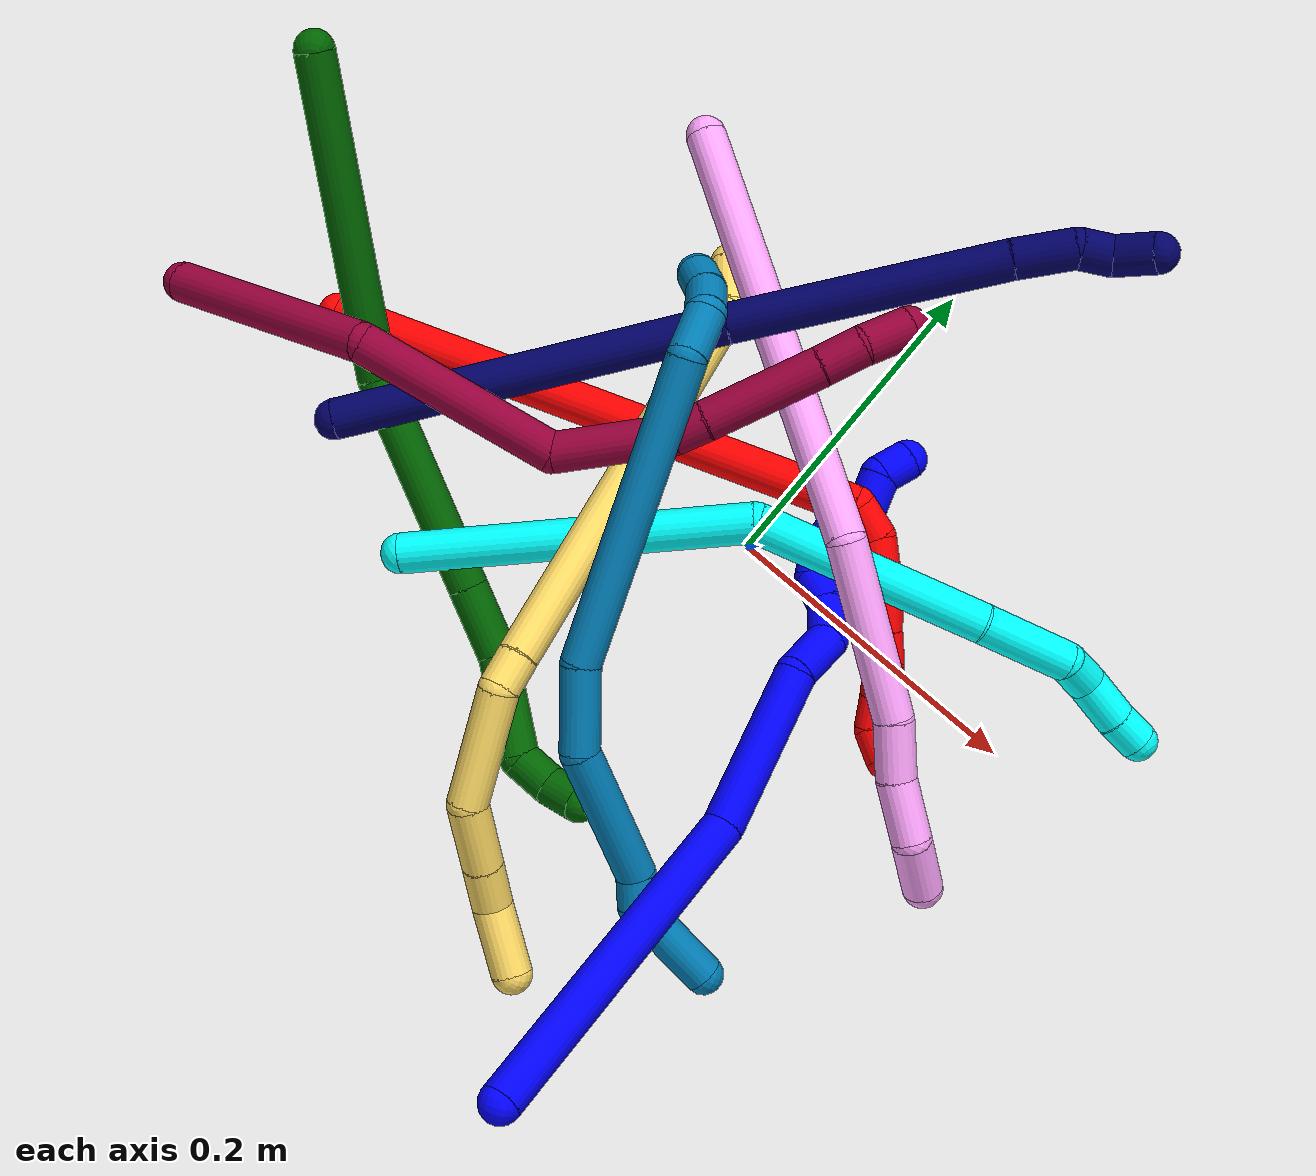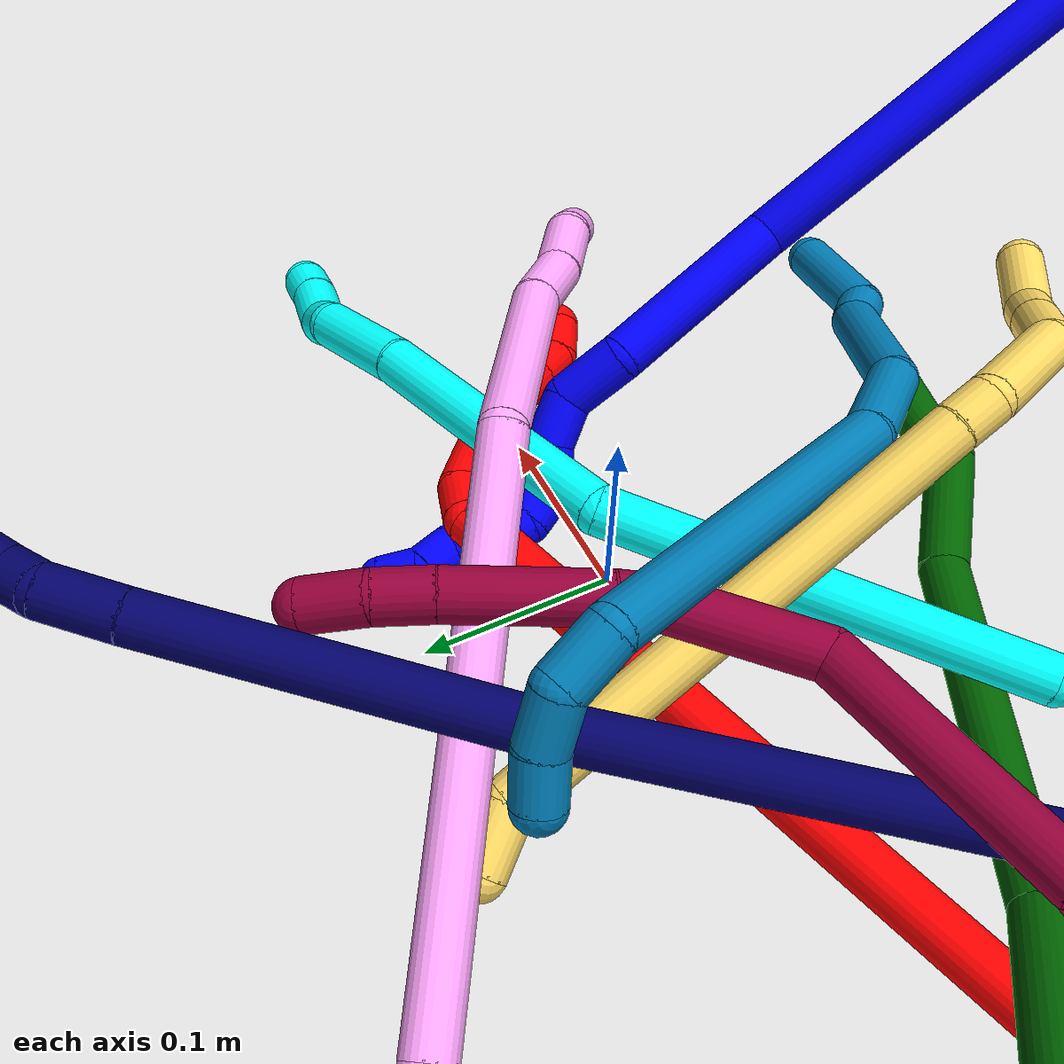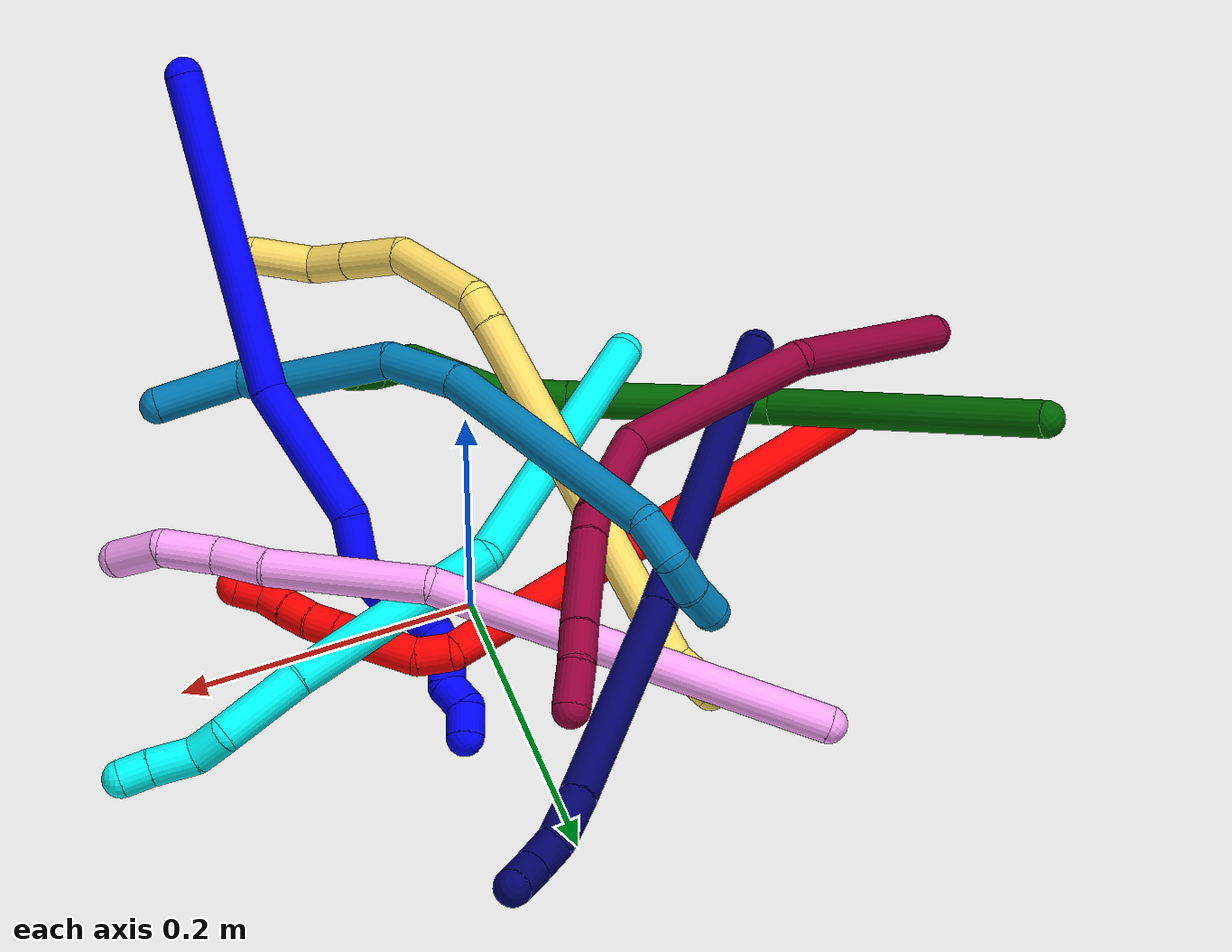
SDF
<sdf version="1.7">
 <world name="default">
  <plugin name="TubeGeneratorPlugin" filename="libtube_generator_plugin.so"/>
  <model name="photoneo_s_sensor">
   <static>1</static>
   <pose>0 0 2 1.57079 1.57079 3.14159</pose>
   <link name="link">
    <inertial><mass>0.1</mass></inertial>
    <sensor name="sensor" type="depth">
     <update_rate>30</update_rate>
     <camera>
      <horizontal_fov>1.22</horizontal_fov>
      <image><width>1920</width><height>1200</height><format>B8G8R8</format></image>
      <clip><near>0.1</near><far>4</far></clip>
      <depth_camera><output>points</output></depth_camera>
     </camera>
     <plugin name="camera_plugin" filename="libgazebo_ros_depth_camera.so">
      <baseline>0.2</baseline>
      <alwaysOn>1</alwaysOn>
      <updateRate>0.0</updateRate>
      <cameraName>camera_ir</cameraName>
      <imageTopicName>/camera/color/image_raw</imageTopicName>
      <cameraInfoTopicName>/camera/color/camera_info</cameraInfoTopicName>
      <depthImageTopicName>/camera/depth/image_raw</depthImageTopicName>
      <depthImageCameraInfoTopicName>/camera/depth/camera_info</depthImageCameraInfoTopicName>
      <pointCloudTopicName>/camera/depth/points</pointCloudTopicName>
      <frameName>fr_optical</frameName>
      <pointCloudCutoff>0.1</pointCloudCutoff>
      <pointCloudCutoffMax>2.0</pointCloudCutoffMax>
      <distortionK1>0</distortionK1>
      <distortionK2>0</distortionK2>
      <distortionK3>0</distortionK3>
      <distortionT1>0</distortionT1>
      <distortionT2>0</distortionT2>
      <CxPrime>0</CxPrime>
      <Cx>0</Cx>
      <Cy>0</Cy>
      <focalLength>0</focalLength>
      <hackBaseline>0</hackBaseline>
     </plugin>
    </sensor>
   </link>
  </model>
  <gravity>0 0 -9.8</gravity>
  <magnetic_field>6e-06 2.3e-05 -4.2e-05</magnetic_field>
  <atmosphere type="adiabatic"/>
  <physics name="default_physics" default="0" type="ode">
   <max_step_size>0.003</max_step_size>
   <real_time_factor>1</real_time_factor>
   <real_time_update_rate>1000</real_time_update_rate>
   <max_contacts>10000</max_contacts>
   <ode>
    <solver>
     <type>quick</type>
     <iters>100</iters>
     <sor>1.3</sor>
     <use_dynamic_moi_rescaling>0</use_dynamic_moi_rescaling>
    </solver>
    <constraints>
     <contact_max_correcting_vel>0</contact_max_correcting_vel>
     <contact_surface_layer>0.001</contact_surface_layer>
     <cfm>0</cfm>
     <erp>0.2</erp>
    </constraints>
   </ode>
  </physics>
  <scene><ambient>0.4 0.4 0.4 1</ambient><background>0.7 0.7 0.7 1</background><shadows>0</shadows></scene>
  <audio><device>default</device></audio>
  <spherical_coordinates>
   <surface_model>EARTH_WGS84</surface_model>
   <latitude_deg>0</latitude_deg>
   <longitude_deg>0</longitude_deg>
   <elevation>0</elevation>
   <heading_deg>0</heading_deg>
  </spherical_coordinates>
  <model name="bin">
   <static>1</static>
   <link name="bottom">
    <collision name="collision-bottom">
     <pose>0 0 -0.01 0 -0 0</pose>
     <geometry><box><size>0.8 0.6 0.02</size></box></geometry>
     <surface>
      <friction><ode><mu>100</mu><mu2>100</mu2></ode></friction>
      <contact><collide_bitmask>65535</collide_bitmask></contact>
     </surface>
    </collision>
   </link>
   <link name="west_wall">
    <collision name="collision-west_wall">
     <pose>-0.41 0 0.1 0 -0 0</pose>
     <geometry><box><size>0.02 0.6 0.2</size></box></geometry>
     <surface>
      <friction><ode><mu>100</mu><mu2>100</mu2></ode></friction>
      <contact><collide_bitmask>65535</collide_bitmask></contact>
     </surface>
    </collision>
   </link>
   <link name="east_wall">
    <collision name="collision-east_wall">
     <pose>0.41 0 0.1 0 -0 0</pose>
     <geometry><box><size>0.02 0.6 0.2</size></box></geometry>
     <surface>
      <friction><ode><mu>100</mu><mu2>100</mu2></ode></friction>
      <contact><collide_bitmask>65535</collide_bitmask></contact>
     </surface>
    </collision>
   </link>
   <link name="south_wall">
    <collision name="collision-south_wall">
     <pose>0 -0.31 0.1 0 -0 0</pose>
     <geometry><box><size>0.8 0.02 0.2</size></box></geometry>
     <surface>
      <friction><ode><mu>100</mu><mu2>100</mu2></ode></friction>
      <contact><collide_bitmask>65535</collide_bitmask></contact>
     </surface>
    </collision>
   </link>
   <link name="north_wall">
    <collision name="collision-north_wall">
     <pose>0 0.31 0.1 0 -0 0</pose>
     <geometry><box><size>0.8 0.02 0.2</size></box></geometry>
     <surface>
      <friction><ode><mu>100</mu><mu2>100</mu2></ode></friction>
      <contact><collide_bitmask>65535</collide_bitmask></contact>
     </surface>
    </collision>
   </link>
  </model>
  <model name="1">
   <static>0</static>
   <link name="1">
    <collision name="collision-cylinder-e_1_1_4">
     <pose>-0.036711 0.092168 -0.041625 -1.995 -0.348209 0.531938</pose>
     <geometry><cylinder><radius>0.0125</radius><length>0.215176</length></cylinder></geometry>
     <surface>
      <friction><ode><mu>1.16</mu><mu2>1.16</mu2><slip1>0</slip1><slip2>0</slip2></ode></friction>
      <contact><ode><kp>1e+06</kp><kd>1</kd><max_vel>0</max_vel><min_depth>0.001</min_depth></ode></contact>
     </surface>
    </collision>
    <visual name="visual-cylinder-e_1_1_4">
     <pose>-0.036711 0.092168 -0.041625 -1.995 -0.348209 0.531938</pose>
     <geometry><cylinder><radius>0.0125</radius><length>0.215176</length></cylinder></geometry>
     <material><ambient>0 0 1 1</ambient></material>
    </visual>
    <collision name="collision-cylinder-e_2_4_5">
     <pose>-0.074927 0.234196 -0.09264 -1.75696 -0.029669 0.035778</pose>
     <geometry><cylinder><radius>0.0125</radius><length>0.101518</length></cylinder></geometry>
     <surface>
      <friction><ode><mu>1.16</mu><mu2>1.16</mu2><slip1>0</slip1><slip2>0</slip2></ode></friction>
      <contact><ode><kp>1e+06</kp><kd>1</kd><max_vel>0</max_vel><min_depth>0.001</min_depth></ode></contact>
     </surface>
    </collision>
    <visual name="visual-cylinder-e_2_4_5">
     <pose>-0.074927 0.234196 -0.09264 -1.75696 -0.029669 0.035778</pose>
     <geometry><cylinder><radius>0.0125</radius><length>0.101518</length></cylinder></geometry>
     <material><ambient>0 0 1 1</ambient></material>
    </visual>
    <collision name="collision-cylinder-e_3_5_6">
     <pose>-0.083049 0.297911 -0.1094 -2.05958 -0.39897 0.649215</pose>
     <geometry><cylinder><radius>0.0125</radius><length>0.034061</length></cylinder></geometry>
     <surface>
      <friction><ode><mu>1.16</mu><mu2>1.16</mu2><slip1>0</slip1><slip2>0</slip2></ode></friction>
      <contact><ode><kp>1e+06</kp><kd>1</kd><max_vel>0</max_vel><min_depth>0.001</min_depth></ode></contact>
     </surface>
    </collision>
    <visual name="visual-cylinder-e_3_5_6">
     <pose>-0.083049 0.297911 -0.1094 -2.05958 -0.39897 0.649215</pose>
     <geometry><cylinder><radius>0.0125</radius><length>0.034061</length></cylinder></geometry>
     <material><ambient>0 0 1 1</ambient></material>
    </visual>
    <collision name="collision-cylinder-e_4_6_7">
     <pose>-0.095521 0.323242 -0.114994 -1.41739 -0.467122 0.402373</pose>
     <geometry><cylinder><radius>0.0125</radius><length>0.026011</length></cylinder></geometry>
     <surface>
      <friction><ode><mu>1.16</mu><mu2>1.16</mu2><slip1>0</slip1><slip2>0</slip2></ode></friction>
      <contact><ode><kp>1e+06</kp><kd>1</kd><max_vel>0</max_vel><min_depth>0.001</min_depth></ode></contact>
     </surface>
    </collision>
    <visual name="visual-cylinder-e_4_6_7">
     <pose>-0.095521 0.323242 -0.114994 -1.41739 -0.467122 0.402373</pose>
     <geometry><cylinder><radius>0.0125</radius><length>0.026011</length></cylinder></geometry>
     <material><ambient>0 0 1 1</ambient></material>
    </visual>
    <collision name="collision-cylinder-e_5_7_8">
     <pose>-0.10629 0.342576 -0.10764 -0.953354 -0.471395 0.246776</pose>
     <geometry><cylinder><radius>0.0125</radius><length>0.021636</length></cylinder></geometry>
     <surface>
      <friction><ode><mu>1.16</mu><mu2>1.16</mu2><slip1>0</slip1><slip2>0</slip2></ode></friction>
      <contact><ode><kp>1e+06</kp><kd>1</kd><max_vel>0</max_vel><min_depth>0.001</min_depth></ode></contact>
     </surface>
    </collision>
    <visual name="visual-cylinder-e_5_7_8">
     <pose>-0.10629 0.342576 -0.10764 -0.953354 -0.471395 0.246776</pose>
     <geometry><cylinder><radius>0.0125</radius><length>0.021636</length></cylinder></geometry>
     <material><ambient>0 0 1 1</ambient></material>
    </visual>
    <collision name="collision-cylinder-e_6_8_9">
     <pose>-0.112171 0.360586 -0.101694 -1.53479 -0.095008 0.091652</pose>
     <geometry><cylinder><radius>0.0125</radius><length>0.020408</length></cylinder></geometry>
     <surface>
      <friction><ode><mu>1.16</mu><mu2>1.16</mu2><slip1>0</slip1><slip2>0</slip2></ode></friction>
      <contact><ode><kp>1e+06</kp><kd>1</kd><max_vel>0</max_vel><min_depth>0.001</min_depth></ode></contact>
     </surface>
    </collision>
    <visual name="visual-cylinder-e_6_8_9">
     <pose>-0.112171 0.360586 -0.101694 -1.53479 -0.095008 0.091652</pose>
     <geometry><cylinder><radius>0.0125</radius><length>0.020408</length></cylinder></geometry>
     <material><ambient>0 0 1 1</ambient></material>
    </visual>
    <collision name="collision-cylinder-e_7_9_10">
     <pose>-0.1124 0.380293 -0.104819 -1.92104 0.072528 -0.103662</pose>
     <geometry><cylinder><radius>0.0125</radius><length>0.020401</length></cylinder></geometry>
     <surface>
      <friction><ode><mu>1.16</mu><mu2>1.16</mu2><slip1>0</slip1><slip2>0</slip2></ode></friction>
      <contact><ode><kp>1e+06</kp><kd>1</kd><max_vel>0</max_vel><min_depth>0.001</min_depth></ode></contact>
     </surface>
    </collision>
    <visual name="visual-cylinder-e_7_9_10">
     <pose>-0.1124 0.380293 -0.104819 -1.92104 0.072528 -0.103662</pose>
     <geometry><cylinder><radius>0.0125</radius><length>0.020401</length></cylinder></geometry>
     <material><ambient>0 0 1 1</ambient></material>
    </visual>
    <collision name="collision-cylinder-e_8_10_11">
     <pose>-0.111772 0.397128 -0.115282 -2.33471 -0.011017 0.025807</pose>
     <geometry><cylinder><radius>0.0125</radius><length>0.020159</length></cylinder></geometry>
     <surface>
      <friction><ode><mu>1.16</mu><mu2>1.16</mu2><slip1>0</slip1><slip2>0</slip2></ode></friction>
      <contact><ode><kp>1e+06</kp><kd>1</kd><max_vel>0</max_vel><min_depth>0.001</min_depth></ode></contact>
     </surface>
    </collision>
    <visual name="visual-cylinder-e_8_10_11">
     <pose>-0.111772 0.397128 -0.115282 -2.33471 -0.011017 0.025807</pose>
     <geometry><cylinder><radius>0.0125</radius><length>0.020159</length></cylinder></geometry>
     <material><ambient>0 0 1 1</ambient></material>
    </visual>
    <collision name="collision-cylinder-e_9_11_12">
     <pose>-0.109731 0.414259 -0.123379 -1.68444 0.213667 -0.239209</pose>
     <geometry><cylinder><radius>0.0125</radius><length>0.020295</length></cylinder></geometry>
     <surface>
      <friction><ode><mu>1.16</mu><mu2>1.16</mu2><slip1>0</slip1><slip2>0</slip2></ode></friction>
      <contact><ode><kp>1e+06</kp><kd>1</kd><max_vel>0</max_vel><min_depth>0.001</min_depth></ode></contact>
     </surface>
    </collision>
    <visual name="visual-cylinder-e_9_11_12">
     <pose>-0.109731 0.414259 -0.123379 -1.68444 0.213667 -0.239209</pose>
     <geometry><cylinder><radius>0.0125</radius><length>0.020295</length></cylinder></geometry>
     <material><ambient>0 0 1 1</ambient></material>
    </visual>
    <collision name="collision-cylinder-e_10_12_2">
     <pose>-0.108413 0.431447 -0.131495 -2.33218 -0.082062 0.1911</pose>
     <geometry><cylinder><radius>0.0125</radius><length>0.020336</length></cylinder></geometry>
     <surface>
      <friction><ode><mu>1.16</mu><mu2>1.16</mu2><slip1>0</slip1><slip2>0</slip2></ode></friction>
      <contact><ode><kp>1e+06</kp><kd>1</kd><max_vel>0</max_vel><min_depth>0.001</min_depth></ode></contact>
     </surface>
    </collision>
    <visual name="visual-cylinder-e_10_12_2">
     <pose>-0.108413 0.431447 -0.131495 -2.33218 -0.082062 0.1911</pose>
     <geometry><cylinder><radius>0.0125</radius><length>0.020336</length></cylinder></geometry>
     <material><ambient>0 0 1 1</ambient></material>
    </visual>
    <collision name="collision-sphere-2">
     <pose>-0.109246 0.438782 -0.138487 0 -0 0</pose>
     <geometry><sphere><radius>0.0125</radius></sphere></geometry>
     <surface>
      <friction><ode><mu>1.16</mu><mu2>1.16</mu2><slip1>0</slip1><slip2>0</slip2></ode></friction>
      <contact><ode><kp>1e+06</kp><kd>1</kd><max_vel>0</max_vel><min_depth>0.001</min_depth></ode></contact>
     </surface>
    </collision>
    <visual name="visual-sphere-2">
     <pose>-0.109246 0.438782 -0.138487 0 -0 0</pose>
     <geometry><sphere><radius>0.0125</radius></sphere></geometry>
     <material><ambient>0 0 1 1</ambient></material>
    </visual>
    <collision name="collision-sphere-12">
     <pose>-0.107579 0.424111 -0.124503 0 -0 0</pose>
     <geometry><sphere><radius>0.0125</radius></sphere></geometry>
     <surface>
      <friction><ode><mu>1.16</mu><mu2>1.16</mu2><slip1>0</slip1><slip2>0</slip2></ode></friction>
      <contact><ode><kp>1e+06</kp><kd>1</kd><max_vel>0</max_vel><min_depth>0.001</min_depth></ode></contact>
     </surface>
    </collision>
    <visual name="visual-sphere-12">
     <pose>-0.107579 0.424111 -0.124503 0 -0 0</pose>
     <geometry><sphere><radius>0.0125</radius></sphere></geometry>
     <material><ambient>0 0 1 1</ambient></material>
    </visual>
    <collision name="collision-sphere-11">
     <pose>-0.111883 0.404406 -0.122254 0 -0 0</pose>
     <geometry><sphere><radius>0.0125</radius></sphere></geometry>
     <surface>
      <friction><ode><mu>1.16</mu><mu2>1.16</mu2><slip1>0</slip1><slip2>0</slip2></ode></friction>
      <contact><ode><kp>1e+06</kp><kd>1</kd><max_vel>0</max_vel><min_depth>0.001</min_depth></ode></contact>
     </surface>
    </collision>
    <visual name="visual-sphere-11">
     <pose>-0.111883 0.404406 -0.122254 0 -0 0</pose>
     <geometry><sphere><radius>0.0125</radius></sphere></geometry>
     <material><ambient>0 0 1 1</ambient></material>
    </visual>
    <collision name="collision-sphere-10">
     <pose>-0.111661 0.389849 -0.10831 0 -0 0</pose>
     <geometry><sphere><radius>0.0125</radius></sphere></geometry>
     <surface>
      <friction><ode><mu>1.16</mu><mu2>1.16</mu2><slip1>0</slip1><slip2>0</slip2></ode></friction>
      <contact><ode><kp>1e+06</kp><kd>1</kd><max_vel>0</max_vel><min_depth>0.001</min_depth></ode></contact>
     </surface>
    </collision>
    <visual name="visual-sphere-10">
     <pose>-0.111661 0.389849 -0.10831 0 -0 0</pose>
     <geometry><sphere><radius>0.0125</radius></sphere></geometry>
     <material><ambient>0 0 1 1</ambient></material>
    </visual>
    <collision name="collision-sphere-9">
     <pose>-0.113139 0.370737 -0.101329 0 -0 0</pose>
     <geometry><sphere><radius>0.0125</radius></sphere></geometry>
     <surface>
      <friction><ode><mu>1.16</mu><mu2>1.16</mu2><slip1>0</slip1><slip2>0</slip2></ode></friction>
      <contact><ode><kp>1e+06</kp><kd>1</kd><max_vel>0</max_vel><min_depth>0.001</min_depth></ode></contact>
     </surface>
    </collision>
    <visual name="visual-sphere-9">
     <pose>-0.113139 0.370737 -0.101329 0 -0 0</pose>
     <geometry><sphere><radius>0.0125</radius></sphere></geometry>
     <material><ambient>0 0 1 1</ambient></material>
    </visual>
    <collision name="collision-sphere-4">
     <pose>-0.073421 0.184336 -0.08325 0 -0 0</pose>
     <geometry><sphere><radius>0.0125</radius></sphere></geometry>
     <surface>
      <friction><ode><mu>1.16</mu><mu2>1.16</mu2><slip1>0</slip1><slip2>0</slip2></ode></friction>
      <contact><ode><kp>1e+06</kp><kd>1</kd><max_vel>0</max_vel><min_depth>0.001</min_depth></ode></contact>
     </surface>
    </collision>
    <visual name="visual-sphere-4">
     <pose>-0.073421 0.184336 -0.08325 0 -0 0</pose>
     <geometry><sphere><radius>0.0125</radius></sphere></geometry>
     <material><ambient>0 0 1 1</ambient></material>
    </visual>
    <collision name="collision-sphere-1">
     <geometry><sphere><radius>0.0125</radius></sphere></geometry>
     <surface>
      <friction><ode><mu>1.16</mu><mu2>1.16</mu2><slip1>0</slip1><slip2>0</slip2></ode></friction>
      <contact><ode><kp>1e+06</kp><kd>1</kd><max_vel>0</max_vel><min_depth>0.001</min_depth></ode></contact>
     </surface>
    </collision>
    <visual name="visual-sphere-1">
     <geometry><sphere><radius>0.0125</radius></sphere></geometry>
     <material><ambient>0 0 1 1</ambient></material>
    </visual>
    <collision name="collision-sphere-8">
     <pose>-0.111203 0.350435 -0.10206 0 -0 0</pose>
     <geometry><sphere><radius>0.0125</radius></sphere></geometry>
     <surface>
      <friction><ode><mu>1.16</mu><mu2>1.16</mu2><slip1>0</slip1><slip2>0</slip2></ode></friction>
      <contact><ode><kp>1e+06</kp><kd>1</kd><max_vel>0</max_vel><min_depth>0.001</min_depth></ode></contact>
     </surface>
    </collision>
    <visual name="visual-sphere-8">
     <pose>-0.111203 0.350435 -0.10206 0 -0 0</pose>
     <geometry><sphere><radius>0.0125</radius></sphere></geometry>
     <material><ambient>0 0 1 1</ambient></material>
    </visual>
    <collision name="collision-sphere-5">
     <pose>-0.076433 0.284056 -0.102031 0 -0 0</pose>
     <geometry><sphere><radius>0.0125</radius></sphere></geometry>
     <surface>
      <friction><ode><mu>1.16</mu><mu2>1.16</mu2><slip1>0</slip1><slip2>0</slip2></ode></friction>
      <contact><ode><kp>1e+06</kp><kd>1</kd><max_vel>0</max_vel><min_depth>0.001</min_depth></ode></contact>
     </surface>
    </collision>
    <visual name="visual-sphere-5">
     <pose>-0.076433 0.284056 -0.102031 0 -0 0</pose>
     <geometry><sphere><radius>0.0125</radius></sphere></geometry>
     <material><ambient>0 0 1 1</ambient></material>
    </visual>
    <collision name="collision-sphere-6">
     <pose>-0.089664 0.311766 -0.116769 0 -0 0</pose>
     <geometry><sphere><radius>0.0125</radius></sphere></geometry>
     <surface>
      <friction><ode><mu>1.16</mu><mu2>1.16</mu2><slip1>0</slip1><slip2>0</slip2></ode></friction>
      <contact><ode><kp>1e+06</kp><kd>1</kd><max_vel>0</max_vel><min_depth>0.001</min_depth></ode></contact>
     </surface>
    </collision>
    <visual name="visual-sphere-6">
     <pose>-0.089664 0.311766 -0.116769 0 -0 0</pose>
     <geometry><sphere><radius>0.0125</radius></sphere></geometry>
     <material><ambient>0 0 1 1</ambient></material>
    </visual>
    <collision name="collision-sphere-7">
     <pose>-0.101378 0.334717 -0.11322 0 -0 0</pose>
     <geometry><sphere><radius>0.0125</radius></sphere></geometry>
     <surface>
      <friction><ode><mu>1.16</mu><mu2>1.16</mu2><slip1>0</slip1><slip2>0</slip2></ode></friction>
      <contact><ode><kp>1e+06</kp><kd>1</kd><max_vel>0</max_vel><min_depth>0.001</min_depth></ode></contact>
     </surface>
    </collision>
    <visual name="visual-sphere-7">
     <pose>-0.101378 0.334717 -0.11322 0 -0 0</pose>
     <geometry><sphere><radius>0.0125</radius></sphere></geometry>
     <material><ambient>0 0 1 1</ambient></material>
    </visual>
    <inertial>
     <pose>-0.068772 0.219756 -0.078247 0 -0 0</pose>
     <mass>0.5</mass>
     <inertia>
      <ixx>0.001183</ixx>
      <ixy>0</ixy>
      <ixz>0</ixz>
      <iyy>0.000258</iyy>
      <iyz>0</iyz>
      <izz>-0.00054</izz>
     </inertia>
    </inertial>
   </link>
   <pose>0.083391 -0.316042 0.224074 -1.4423 -1.33363 1.8641</pose>
  </model>
  <model name="2">
   <static>0</static>
   <link name="2">
    <collision name="collision-cylinder-e_1_1_4">
     <pose>0.116093 0.066121 0.104433 -0.564434 0.754066 -0.22863</pose>
     <geometry><cylinder><radius>0.0125</radius><length>0.339151</length></cylinder></geometry>
     <surface>
      <friction><ode><mu>1.16</mu><mu2>1.16</mu2><slip1>0</slip1><slip2>0</slip2></ode></friction>
      <contact><ode><kp>1e+06</kp><kd>1</kd><max_vel>0</max_vel><min_depth>0.001</min_depth></ode></contact>
     </surface>
    </collision>
    <visual name="visual-cylinder-e_1_1_4">
     <pose>0.116093 0.066121 0.104433 -0.564434 0.754066 -0.22863</pose>
     <geometry><cylinder><radius>0.0125</radius><length>0.339151</length></cylinder></geometry>
     <material><ambient>1 0 0 1</ambient></material>
    </visual>
    <collision name="collision-cylinder-e_2_4_5">
     <pose>0.242178 0.129543 0.213977 0.486071 1.04643 0.284113</pose>
     <geometry><cylinder><radius>0.0125</radius><length>0.023086</length></cylinder></geometry>
     <surface>
      <friction><ode><mu>1.16</mu><mu2>1.16</mu2><slip1>0</slip1><slip2>0</slip2></ode></friction>
      <contact><ode><kp>1e+06</kp><kd>1</kd><max_vel>0</max_vel><min_depth>0.001</min_depth></ode></contact>
     </surface>
    </collision>
    <visual name="visual-cylinder-e_2_4_5">
     <pose>0.242178 0.129543 0.213977 0.486071 1.04643 0.284113</pose>
     <geometry><cylinder><radius>0.0125</radius><length>0.023086</length></cylinder></geometry>
     <material><ambient>1 0 0 1</ambient></material>
    </visual>
    <collision name="collision-cylinder-e_3_5_6">
     <pose>0.262906 0.11622 0.226399 0.967955 0.694199 0.375835</pose>
     <geometry><cylinder><radius>0.0125</radius><length>0.03356</length></cylinder></geometry>
     <surface>
      <friction><ode><mu>1.16</mu><mu2>1.16</mu2><slip1>0</slip1><slip2>0</slip2></ode></friction>
      <contact><ode><kp>1e+06</kp><kd>1</kd><max_vel>0</max_vel><min_depth>0.001</min_depth></ode></contact>
     </surface>
    </collision>
    <visual name="visual-cylinder-e_3_5_6">
     <pose>0.262906 0.11622 0.226399 0.967955 0.694199 0.375835</pose>
     <geometry><cylinder><radius>0.0125</radius><length>0.03356</length></cylinder></geometry>
     <material><ambient>1 0 0 1</ambient></material>
    </visual>
    <collision name="collision-cylinder-e_4_6_7">
     <pose>0.280925 0.097233 0.237087 1.18712 0.6794 0.468153</pose>
     <geometry><cylinder><radius>0.0125</radius><length>0.023186</length></cylinder></geometry>
     <surface>
      <friction><ode><mu>1.16</mu><mu2>1.16</mu2><slip1>0</slip1><slip2>0</slip2></ode></friction>
      <contact><ode><kp>1e+06</kp><kd>1</kd><max_vel>0</max_vel><min_depth>0.001</min_depth></ode></contact>
     </surface>
    </collision>
    <visual name="visual-cylinder-e_4_6_7">
     <pose>0.280925 0.097233 0.237087 1.18712 0.6794 0.468153</pose>
     <geometry><cylinder><radius>0.0125</radius><length>0.023186</length></cylinder></geometry>
     <material><ambient>1 0 0 1</ambient></material>
    </visual>
    <collision name="collision-cylinder-e_5_7_8">
     <pose>0.295036 0.081849 0.244081 1.09502 0.71272 0.446352</pose>
     <geometry><cylinder><radius>0.0125</radius><length>0.020879</length></cylinder></geometry>
     <surface>
      <friction><ode><mu>1.16</mu><mu2>1.16</mu2><slip1>0</slip1><slip2>0</slip2></ode></friction>
      <contact><ode><kp>1e+06</kp><kd>1</kd><max_vel>0</max_vel><min_depth>0.001</min_depth></ode></contact>
     </surface>
    </collision>
    <visual name="visual-cylinder-e_5_7_8">
     <pose>0.295036 0.081849 0.244081 1.09502 0.71272 0.446352</pose>
     <geometry><cylinder><radius>0.0125</radius><length>0.020879</length></cylinder></geometry>
     <material><ambient>1 0 0 1</ambient></material>
    </visual>
    <collision name="collision-cylinder-e_6_8_9">
     <pose>0.307267 0.066893 0.250591 1.22115 0.569334 0.403943</pose>
     <geometry><cylinder><radius>0.0125</radius><length>0.020055</length></cylinder></geometry>
     <surface>
      <friction><ode><mu>1.16</mu><mu2>1.16</mu2><slip1>0</slip1><slip2>0</slip2></ode></friction>
      <contact><ode><kp>1e+06</kp><kd>1</kd><max_vel>0</max_vel><min_depth>0.001</min_depth></ode></contact>
     </surface>
    </collision>
    <visual name="visual-cylinder-e_6_8_9">
     <pose>0.307267 0.066893 0.250591 1.22115 0.569334 0.403943</pose>
     <geometry><cylinder><radius>0.0125</radius><length>0.020055</length></cylinder></geometry>
     <material><ambient>1 0 0 1</ambient></material>
    </visual>
    <collision name="collision-cylinder-e_7_9_10">
     <pose>0.317571 0.050666 0.256226 1.25149 0.5111 0.373191</pose>
     <geometry><cylinder><radius>0.0125</radius><length>0.020027</length></cylinder></geometry>
     <surface>
      <friction><ode><mu>1.16</mu><mu2>1.16</mu2><slip1>0</slip1><slip2>0</slip2></ode></friction>
      <contact><ode><kp>1e+06</kp><kd>1</kd><max_vel>0</max_vel><min_depth>0.001</min_depth></ode></contact>
     </surface>
    </collision>
    <visual name="visual-cylinder-e_7_9_10">
     <pose>0.317571 0.050666 0.256226 1.25149 0.5111 0.373191</pose>
     <geometry><cylinder><radius>0.0125</radius><length>0.020027</length></cylinder></geometry>
     <material><ambient>1 0 0 1</ambient></material>
    </visual>
    <collision name="collision-cylinder-e_8_10_2">
     <pose>0.328228 0.038142 0.266003 0.541525 0.611713 0.174853</pose>
     <geometry><cylinder><radius>0.0125</radius><length>0.020055</length></cylinder></geometry>
     <surface>
      <friction><ode><mu>1.16</mu><mu2>1.16</mu2><slip1>0</slip1><slip2>0</slip2></ode></friction>
      <contact><ode><kp>1e+06</kp><kd>1</kd><max_vel>0</max_vel><min_depth>0.001</min_depth></ode></contact>
     </surface>
    </collision>
    <visual name="visual-cylinder-e_8_10_2">
     <pose>0.328228 0.038142 0.266003 0.541525 0.611713 0.174853</pose>
     <geometry><cylinder><radius>0.0125</radius><length>0.020055</length></cylinder></geometry>
     <material><ambient>1 0 0 1</ambient></material>
    </visual>
    <collision name="collision-sphere-2">
     <pose>0.333986 0.033911 0.273037 0 -0 0</pose>
     <geometry><sphere><radius>0.0125</radius></sphere></geometry>
     <surface>
      <friction><ode><mu>1.16</mu><mu2>1.16</mu2><slip1>0</slip1><slip2>0</slip2></ode></friction>
      <contact><ode><kp>1e+06</kp><kd>1</kd><max_vel>0</max_vel><min_depth>0.001</min_depth></ode></contact>
     </surface>
    </collision>
    <visual name="visual-sphere-2">
     <pose>0.333986 0.033911 0.273037 0 -0 0</pose>
     <geometry><sphere><radius>0.0125</radius></sphere></geometry>
     <material><ambient>1 0 0 1</ambient></material>
    </visual>
    <collision name="collision-sphere-10">
     <pose>0.322469 0.042374 0.258968 0 -0 0</pose>
     <geometry><sphere><radius>0.0125</radius></sphere></geometry>
     <surface>
      <friction><ode><mu>1.16</mu><mu2>1.16</mu2><slip1>0</slip1><slip2>0</slip2></ode></friction>
      <contact><ode><kp>1e+06</kp><kd>1</kd><max_vel>0</max_vel><min_depth>0.001</min_depth></ode></contact>
     </surface>
    </collision>
    <visual name="visual-sphere-10">
     <pose>0.322469 0.042374 0.258968 0 -0 0</pose>
     <geometry><sphere><radius>0.0125</radius></sphere></geometry>
     <material><ambient>1 0 0 1</ambient></material>
    </visual>
    <collision name="collision-sphere-9">
     <pose>0.312673 0.058959 0.253485 0 -0 0</pose>
     <geometry><sphere><radius>0.0125</radius></sphere></geometry>
     <surface>
      <friction><ode><mu>1.16</mu><mu2>1.16</mu2><slip1>0</slip1><slip2>0</slip2></ode></friction>
      <contact><ode><kp>1e+06</kp><kd>1</kd><max_vel>0</max_vel><min_depth>0.001</min_depth></ode></contact>
     </surface>
    </collision>
    <visual name="visual-sphere-9">
     <pose>0.312673 0.058959 0.253485 0 -0 0</pose>
     <geometry><sphere><radius>0.0125</radius></sphere></geometry>
     <material><ambient>1 0 0 1</ambient></material>
    </visual>
    <collision name="collision-sphere-4">
     <pose>0.232186 0.132243 0.208867 0 -0 0</pose>
     <geometry><sphere><radius>0.0125</radius></sphere></geometry>
     <surface>
      <friction><ode><mu>1.16</mu><mu2>1.16</mu2><slip1>0</slip1><slip2>0</slip2></ode></friction>
      <contact><ode><kp>1e+06</kp><kd>1</kd><max_vel>0</max_vel><min_depth>0.001</min_depth></ode></contact>
     </surface>
    </collision>
    <visual name="visual-sphere-4">
     <pose>0.232186 0.132243 0.208867 0 -0 0</pose>
     <geometry><sphere><radius>0.0125</radius></sphere></geometry>
     <material><ambient>1 0 0 1</ambient></material>
    </visual>
    <collision name="collision-sphere-1">
     <geometry><sphere><radius>0.0125</radius></sphere></geometry>
     <surface>
      <friction><ode><mu>1.16</mu><mu2>1.16</mu2><slip1>0</slip1><slip2>0</slip2></ode></friction>
      <contact><ode><kp>1e+06</kp><kd>1</kd><max_vel>0</max_vel><min_depth>0.001</min_depth></ode></contact>
     </surface>
    </collision>
    <visual name="visual-sphere-1">
     <geometry><sphere><radius>0.0125</radius></sphere></geometry>
     <material><ambient>1 0 0 1</ambient></material>
    </visual>
    <collision name="collision-sphere-8">
     <pose>0.301862 0.074828 0.247698 0 -0 0</pose>
     <geometry><sphere><radius>0.0125</radius></sphere></geometry>
     <surface>
      <friction><ode><mu>1.16</mu><mu2>1.16</mu2><slip1>0</slip1><slip2>0</slip2></ode></friction>
      <contact><ode><kp>1e+06</kp><kd>1</kd><max_vel>0</max_vel><min_depth>0.001</min_depth></ode></contact>
     </surface>
    </collision>
    <visual name="visual-sphere-8">
     <pose>0.301862 0.074828 0.247698 0 -0 0</pose>
     <geometry><sphere><radius>0.0125</radius></sphere></geometry>
     <material><ambient>1 0 0 1</ambient></material>
    </visual>
    <collision name="collision-sphere-5">
     <pose>0.25217 0.126843 0.219086 0 -0 0</pose>
     <geometry><sphere><radius>0.0125</radius></sphere></geometry>
     <surface>
      <friction><ode><mu>1.16</mu><mu2>1.16</mu2><slip1>0</slip1><slip2>0</slip2></ode></friction>
      <contact><ode><kp>1e+06</kp><kd>1</kd><max_vel>0</max_vel><min_depth>0.001</min_depth></ode></contact>
     </surface>
    </collision>
    <visual name="visual-sphere-5">
     <pose>0.25217 0.126843 0.219086 0 -0 0</pose>
     <geometry><sphere><radius>0.0125</radius></sphere></geometry>
     <material><ambient>1 0 0 1</ambient></material>
    </visual>
    <collision name="collision-sphere-6">
     <pose>0.273641 0.105596 0.233711 0 -0 0</pose>
     <geometry><sphere><radius>0.0125</radius></sphere></geometry>
     <surface>
      <friction><ode><mu>1.16</mu><mu2>1.16</mu2><slip1>0</slip1><slip2>0</slip2></ode></friction>
      <contact><ode><kp>1e+06</kp><kd>1</kd><max_vel>0</max_vel><min_depth>0.001</min_depth></ode></contact>
     </surface>
    </collision>
    <visual name="visual-sphere-6">
     <pose>0.273641 0.105596 0.233711 0 -0 0</pose>
     <geometry><sphere><radius>0.0125</radius></sphere></geometry>
     <material><ambient>1 0 0 1</ambient></material>
    </visual>
    <collision name="collision-sphere-7">
     <pose>0.28821 0.08887 0.240463 0 -0 0</pose>
     <geometry><sphere><radius>0.0125</radius></sphere></geometry>
     <surface>
      <friction><ode><mu>1.16</mu><mu2>1.16</mu2><slip1>0</slip1><slip2>0</slip2></ode></friction>
      <contact><ode><kp>1e+06</kp><kd>1</kd><max_vel>0</max_vel><min_depth>0.001</min_depth></ode></contact>
     </surface>
    </collision>
    <visual name="visual-sphere-7">
     <pose>0.28821 0.08887 0.240463 0 -0 0</pose>
     <geometry><sphere><radius>0.0125</radius></sphere></geometry>
     <material><ambient>1 0 0 1</ambient></material>
    </visual>
    <inertial>
     <pose>0.171131 0.072801 0.148083 0 -0 0</pose>
     <mass>0.5</mass>
     <inertia>
      <ixx>0.001818</ixx>
      <ixy>0</ixy>
      <ixz>0</ixz>
      <iyy>0.002434</iyy>
      <iyz>0</iyz>
      <izz>-0.003486</izz>
     </inertia>
    </inertial>
   </link>
   <pose>-0.28526 -0.05057 0.011489 0.027345 0.635959 -0.049201</pose>
  </model>
  <model name="3">
   <static>0</static>
   <link name="3">
    <collision name="collision-cylinder-e_1_1_4">
     <pose>0.062595 0.066881 0.058111 -0.855447 0.615065 -0.287578</pose>
     <geometry><cylinder><radius>0.0125</radius><length>0.216961</length></cylinder></geometry>
     <surface>
      <friction><ode><mu>1.16</mu><mu2>1.16</mu2><slip1>0</slip1><slip2>0</slip2></ode></friction>
      <contact><ode><kp>1e+06</kp><kd>1</kd><max_vel>0</max_vel><min_depth>0.001</min_depth></ode></contact>
     </surface>
    </collision>
    <visual name="visual-cylinder-e_1_1_4">
     <pose>0.062595 0.066881 0.058111 -0.855447 0.615065 -0.287578</pose>
     <geometry><cylinder><radius>0.0125</radius><length>0.216961</length></cylinder></geometry>
     <material><ambient>0.003922 1 0.996078 1</ambient></material>
    </visual>
    <collision name="collision-cylinder-e_2_4_5">
     <pose>0.159452 0.14835 0.180765 -0.222287 0.477775 -0.054346</pose>
     <geometry><cylinder><radius>0.0125</radius><length>0.149031</length></cylinder></geometry>
     <surface>
      <friction><ode><mu>1.16</mu><mu2>1.16</mu2><slip1>0</slip1><slip2>0</slip2></ode></friction>
      <contact><ode><kp>1e+06</kp><kd>1</kd><max_vel>0</max_vel><min_depth>0.001</min_depth></ode></contact>
     </surface>
    </collision>
    <visual name="visual-cylinder-e_2_4_5">
     <pose>0.159452 0.14835 0.180765 -0.222287 0.477775 -0.054346</pose>
     <geometry><cylinder><radius>0.0125</radius><length>0.149031</length></cylinder></geometry>
     <material><ambient>0.003922 1 0.996078 1</ambient></material>
    </visual>
    <collision name="collision-cylinder-e_3_5_6">
     <pose>0.209665 0.164858 0.270002 -0.077593 0.572158 -0.022834</pose>
     <geometry><cylinder><radius>0.0125</radius><length>0.05892</length></cylinder></geometry>
     <surface>
      <friction><ode><mu>1.16</mu><mu2>1.16</mu2><slip1>0</slip1><slip2>0</slip2></ode></friction>
      <contact><ode><kp>1e+06</kp><kd>1</kd><max_vel>0</max_vel><min_depth>0.001</min_depth></ode></contact>
     </surface>
    </collision>
    <visual name="visual-cylinder-e_3_5_6">
     <pose>0.209665 0.164858 0.270002 -0.077593 0.572158 -0.022834</pose>
     <geometry><cylinder><radius>0.0125</radius><length>0.05892</length></cylinder></geometry>
     <material><ambient>0.003922 1 0.996078 1</ambient></material>
    </visual>
    <collision name="collision-cylinder-e_4_6_7">
     <pose>0.2318 0.161692 0.303793 0.509694 0.535467 0.142684</pose>
     <geometry><cylinder><radius>0.0125</radius><length>0.024238</length></cylinder></geometry>
     <surface>
      <friction><ode><mu>1.16</mu><mu2>1.16</mu2><slip1>0</slip1><slip2>0</slip2></ode></friction>
      <contact><ode><kp>1e+06</kp><kd>1</kd><max_vel>0</max_vel><min_depth>0.001</min_depth></ode></contact>
     </surface>
    </collision>
    <visual name="visual-cylinder-e_4_6_7">
     <pose>0.2318 0.161692 0.303793 0.509694 0.535467 0.142684</pose>
     <geometry><cylinder><radius>0.0125</radius><length>0.024238</length></cylinder></geometry>
     <material><ambient>0.003922 1 0.996078 1</ambient></material>
    </visual>
    <collision name="collision-cylinder-e_5_7_8">
     <pose>0.241003 0.153977 0.327483 0.178308 0.200929 0.018021</pose>
     <geometry><cylinder><radius>0.0125</radius><length>0.030261</length></cylinder></geometry>
     <surface>
      <friction><ode><mu>1.16</mu><mu2>1.16</mu2><slip1>0</slip1><slip2>0</slip2></ode></friction>
      <contact><ode><kp>1e+06</kp><kd>1</kd><max_vel>0</max_vel><min_depth>0.001</min_depth></ode></contact>
     </surface>
    </collision>
    <visual name="visual-cylinder-e_5_7_8">
     <pose>0.241003 0.153977 0.327483 0.178308 0.200929 0.018021</pose>
     <geometry><cylinder><radius>0.0125</radius><length>0.030261</length></cylinder></geometry>
     <material><ambient>0.003922 1 0.996078 1</ambient></material>
    </visual>
    <collision name="collision-cylinder-e_6_8_2">
     <pose>0.246953 0.150023 0.351853 0.134641 0.288552 0.01959</pose>
     <geometry><cylinder><radius>0.0125</radius><length>0.020589</length></cylinder></geometry>
     <surface>
      <friction><ode><mu>1.16</mu><mu2>1.16</mu2><slip1>0</slip1><slip2>0</slip2></ode></friction>
      <contact><ode><kp>1e+06</kp><kd>1</kd><max_vel>0</max_vel><min_depth>0.001</min_depth></ode></contact>
     </surface>
    </collision>
    <visual name="visual-cylinder-e_6_8_2">
     <pose>0.246953 0.150023 0.351853 0.134641 0.288552 0.01959</pose>
     <geometry><cylinder><radius>0.0125</radius><length>0.020589</length></cylinder></geometry>
     <material><ambient>0.003922 1 0.996078 1</ambient></material>
    </visual>
    <collision name="collision-sphere-2">
     <pose>0.249882 0.148698 0.361632 0 -0 0</pose>
     <geometry><sphere><radius>0.0125</radius></sphere></geometry>
     <surface>
      <friction><ode><mu>1.16</mu><mu2>1.16</mu2><slip1>0</slip1><slip2>0</slip2></ode></friction>
      <contact><ode><kp>1e+06</kp><kd>1</kd><max_vel>0</max_vel><min_depth>0.001</min_depth></ode></contact>
     </surface>
    </collision>
    <visual name="visual-sphere-2">
     <pose>0.249882 0.148698 0.361632 0 -0 0</pose>
     <geometry><sphere><radius>0.0125</radius></sphere></geometry>
     <material><ambient>0.003922 1 0.996078 1</ambient></material>
    </visual>
    <collision name="collision-sphere-4">
     <pose>0.125189 0.133762 0.116222 0 -0 0</pose>
     <geometry><sphere><radius>0.0125</radius></sphere></geometry>
     <surface>
      <friction><ode><mu>1.16</mu><mu2>1.16</mu2><slip1>0</slip1><slip2>0</slip2></ode></friction>
      <contact><ode><kp>1e+06</kp><kd>1</kd><max_vel>0</max_vel><min_depth>0.001</min_depth></ode></contact>
     </surface>
    </collision>
    <visual name="visual-sphere-4">
     <pose>0.125189 0.133762 0.116222 0 -0 0</pose>
     <geometry><sphere><radius>0.0125</radius></sphere></geometry>
     <material><ambient>0.003922 1 0.996078 1</ambient></material>
    </visual>
    <collision name="collision-sphere-1">
     <geometry><sphere><radius>0.0125</radius></sphere></geometry>
     <surface>
      <friction><ode><mu>1.16</mu><mu2>1.16</mu2><slip1>0</slip1><slip2>0</slip2></ode></friction>
      <contact><ode><kp>1e+06</kp><kd>1</kd><max_vel>0</max_vel><min_depth>0.001</min_depth></ode></contact>
     </surface>
    </collision>
    <visual name="visual-sphere-1">
     <geometry><sphere><radius>0.0125</radius></sphere></geometry>
     <material><ambient>0.003922 1 0.996078 1</ambient></material>
    </visual>
    <collision name="collision-sphere-8">
     <pose>0.244023 0.151348 0.342074 0 -0 0</pose>
     <geometry><sphere><radius>0.0125</radius></sphere></geometry>
     <surface>
      <friction><ode><mu>1.16</mu><mu2>1.16</mu2><slip1>0</slip1><slip2>0</slip2></ode></friction>
      <contact><ode><kp>1e+06</kp><kd>1</kd><max_vel>0</max_vel><min_depth>0.001</min_depth></ode></contact>
     </surface>
    </collision>
    <visual name="visual-sphere-8">
     <pose>0.244023 0.151348 0.342074 0 -0 0</pose>
     <geometry><sphere><radius>0.0125</radius></sphere></geometry>
     <material><ambient>0.003922 1 0.996078 1</ambient></material>
    </visual>
    <collision name="collision-sphere-5">
     <pose>0.193714 0.162938 0.245308 0 -0 0</pose>
     <geometry><sphere><radius>0.0125</radius></sphere></geometry>
     <surface>
      <friction><ode><mu>1.16</mu><mu2>1.16</mu2><slip1>0</slip1><slip2>0</slip2></ode></friction>
      <contact><ode><kp>1e+06</kp><kd>1</kd><max_vel>0</max_vel><min_depth>0.001</min_depth></ode></contact>
     </surface>
    </collision>
    <visual name="visual-sphere-5">
     <pose>0.193714 0.162938 0.245308 0 -0 0</pose>
     <geometry><sphere><radius>0.0125</radius></sphere></geometry>
     <material><ambient>0.003922 1 0.996078 1</ambient></material>
    </visual>
    <collision name="collision-sphere-6">
     <pose>0.225616 0.166778 0.294696 0 -0 0</pose>
     <geometry><sphere><radius>0.0125</radius></sphere></geometry>
     <surface>
      <friction><ode><mu>1.16</mu><mu2>1.16</mu2><slip1>0</slip1><slip2>0</slip2></ode></friction>
      <contact><ode><kp>1e+06</kp><kd>1</kd><max_vel>0</max_vel><min_depth>0.001</min_depth></ode></contact>
     </surface>
    </collision>
    <visual name="visual-sphere-6">
     <pose>0.225616 0.166778 0.294696 0 -0 0</pose>
     <geometry><sphere><radius>0.0125</radius></sphere></geometry>
     <material><ambient>0.003922 1 0.996078 1</ambient></material>
    </visual>
    <collision name="collision-sphere-7">
     <pose>0.237984 0.156607 0.312891 0 -0 0</pose>
     <geometry><sphere><radius>0.0125</radius></sphere></geometry>
     <surface>
      <friction><ode><mu>1.16</mu><mu2>1.16</mu2><slip1>0</slip1><slip2>0</slip2></ode></friction>
      <contact><ode><kp>1e+06</kp><kd>1</kd><max_vel>0</max_vel><min_depth>0.001</min_depth></ode></contact>
     </surface>
    </collision>
    <visual name="visual-sphere-7">
     <pose>0.237984 0.156607 0.312891 0 -0 0</pose>
     <geometry><sphere><radius>0.0125</radius></sphere></geometry>
     <material><ambient>0.003922 1 0.996078 1</ambient></material>
    </visual>
    <inertial>
     <pose>0.135386 0.116 0.159947 0 -0 0</pose>
     <mass>0.5</mass>
     <inertia>
      <ixx>0.000753</ixx>
      <ixy>0</ixy>
      <ixz>0</ixz>
      <iyy>0.000748</iyy>
      <iyz>0</iyz>
      <izz>-0.001195</izz>
     </inertia>
    </inertial>
   </link>
   <pose>-0.159133 -0.137625 0.037138 1.50416 0.665968 1.30344</pose>
  </model>
  <model name="4">
   <static>0</static>
   <link name="4">
    <collision name="collision-cylinder-e_1_1_4">
     <pose>0.10734 -0.066208 -0.052752 2.24356 0.903017 1.57716</pose>
     <geometry><cylinder><radius>0.0125</radius><length>0.27341</length></cylinder></geometry>
     <surface>
      <friction><ode><mu>1.16</mu><mu2>1.16</mu2><slip1>0</slip1><slip2>0</slip2></ode></friction>
      <contact><ode><kp>1e+06</kp><kd>1</kd><max_vel>0</max_vel><min_depth>0.001</min_depth></ode></contact>
     </surface>
    </collision>
    <visual name="visual-cylinder-e_1_1_4">
     <pose>0.10734 -0.066208 -0.052752 2.24356 0.903017 1.57716</pose>
     <geometry><cylinder><radius>0.0125</radius><length>0.27341</length></cylinder></geometry>
     <material><ambient>1 0.65098 0.996078 1</ambient></material>
    </visual>
    <collision name="collision-cylinder-e_2_4_5">
     <pose>0.238784 -0.169364 -0.139248 2.31091 0.448898 0.955386</pose>
     <geometry><cylinder><radius>0.0125</radius><length>0.111083</length></cylinder></geometry>
     <surface>
      <friction><ode><mu>1.16</mu><mu2>1.16</mu2><slip1>0</slip1><slip2>0</slip2></ode></friction>
      <contact><ode><kp>1e+06</kp><kd>1</kd><max_vel>0</max_vel><min_depth>0.001</min_depth></ode></contact>
     </surface>
    </collision>
    <visual name="visual-cylinder-e_2_4_5">
     <pose>0.238784 -0.169364 -0.139248 2.31091 0.448898 0.955386</pose>
     <geometry><cylinder><radius>0.0125</radius><length>0.111083</length></cylinder></geometry>
     <material><ambient>1 0.65098 0.996078 1</ambient></material>
    </visual>
    <collision name="collision-cylinder-e_3_5_6">
     <pose>0.268851 -0.221294 -0.182131 2.11847 0.327551 0.572546</pose>
     <geometry><cylinder><radius>0.0125</radius><length>0.037068</length></cylinder></geometry>
     <surface>
      <friction><ode><mu>1.16</mu><mu2>1.16</mu2><slip1>0</slip1><slip2>0</slip2></ode></friction>
      <contact><ode><kp>1e+06</kp><kd>1</kd><max_vel>0</max_vel><min_depth>0.001</min_depth></ode></contact>
     </surface>
    </collision>
    <visual name="visual-cylinder-e_3_5_6">
     <pose>0.268851 -0.221294 -0.182131 2.11847 0.327551 0.572546</pose>
     <geometry><cylinder><radius>0.0125</radius><length>0.037068</length></cylinder></geometry>
     <material><ambient>1 0.65098 0.996078 1</ambient></material>
    </visual>
    <collision name="collision-cylinder-e_4_6_7">
     <pose>0.283702 -0.249367 -0.202566 2.28276 0.474772 0.972175</pose>
     <geometry><cylinder><radius>0.0125</radius><length>0.038885</length></cylinder></geometry>
     <surface>
      <friction><ode><mu>1.16</mu><mu2>1.16</mu2><slip1>0</slip1><slip2>0</slip2></ode></friction>
      <contact><ode><kp>1e+06</kp><kd>1</kd><max_vel>0</max_vel><min_depth>0.001</min_depth></ode></contact>
     </surface>
    </collision>
    <visual name="visual-cylinder-e_4_6_7">
     <pose>0.283702 -0.249367 -0.202566 2.28276 0.474772 0.972175</pose>
     <geometry><cylinder><radius>0.0125</radius><length>0.038885</length></cylinder></geometry>
     <material><ambient>1 0.65098 0.996078 1</ambient></material>
    </visual>
    <collision name="collision-cylinder-e_5_7_2">
     <pose>0.292588 -0.275829 -0.228436 2.39919 -5.1e-05 -0.000131</pose>
     <geometry><cylinder><radius>0.0125</radius><length>0.039554</length></cylinder></geometry>
     <surface>
      <friction><ode><mu>1.16</mu><mu2>1.16</mu2><slip1>0</slip1><slip2>0</slip2></ode></friction>
      <contact><ode><kp>1e+06</kp><kd>1</kd><max_vel>0</max_vel><min_depth>0.001</min_depth></ode></contact>
     </surface>
    </collision>
    <visual name="visual-cylinder-e_5_7_2">
     <pose>0.292588 -0.275829 -0.228436 2.39919 -5.1e-05 -0.000131</pose>
     <geometry><cylinder><radius>0.0125</radius><length>0.039554</length></cylinder></geometry>
     <material><ambient>1 0.65098 0.996078 1</ambient></material>
    </visual>
    <collision name="collision-sphere-2">
     <pose>0.292587 -0.2892 -0.243009 0 -0 0</pose>
     <geometry><sphere><radius>0.0125</radius></sphere></geometry>
     <surface>
      <friction><ode><mu>1.16</mu><mu2>1.16</mu2><slip1>0</slip1><slip2>0</slip2></ode></friction>
      <contact><ode><kp>1e+06</kp><kd>1</kd><max_vel>0</max_vel><min_depth>0.001</min_depth></ode></contact>
     </surface>
    </collision>
    <visual name="visual-sphere-2">
     <pose>0.292587 -0.2892 -0.243009 0 -0 0</pose>
     <geometry><sphere><radius>0.0125</radius></sphere></geometry>
     <material><ambient>1 0.65098 0.996078 1</ambient></material>
    </visual>
    <collision name="collision-sphere-7">
     <pose>0.292589 -0.262459 -0.213863 0 -0 0</pose>
     <geometry><sphere><radius>0.0125</radius></sphere></geometry>
     <surface>
      <friction><ode><mu>1.16</mu><mu2>1.16</mu2><slip1>0</slip1><slip2>0</slip2></ode></friction>
      <contact><ode><kp>1e+06</kp><kd>1</kd><max_vel>0</max_vel><min_depth>0.001</min_depth></ode></contact>
     </surface>
    </collision>
    <visual name="visual-sphere-7">
     <pose>0.292589 -0.262459 -0.213863 0 -0 0</pose>
     <geometry><sphere><radius>0.0125</radius></sphere></geometry>
     <material><ambient>1 0.65098 0.996078 1</ambient></material>
    </visual>
    <collision name="collision-sphere-6">
     <pose>0.274814 -0.236276 -0.191268 0 -0 0</pose>
     <geometry><sphere><radius>0.0125</radius></sphere></geometry>
     <surface>
      <friction><ode><mu>1.16</mu><mu2>1.16</mu2><slip1>0</slip1><slip2>0</slip2></ode></friction>
      <contact><ode><kp>1e+06</kp><kd>1</kd><max_vel>0</max_vel><min_depth>0.001</min_depth></ode></contact>
     </surface>
    </collision>
    <visual name="visual-sphere-6">
     <pose>0.274814 -0.236276 -0.191268 0 -0 0</pose>
     <geometry><sphere><radius>0.0125</radius></sphere></geometry>
     <material><ambient>1 0.65098 0.996078 1</ambient></material>
    </visual>
    <collision name="collision-sphere-5">
     <pose>0.262888 -0.206312 -0.172993 0 -0 0</pose>
     <geometry><sphere><radius>0.0125</radius></sphere></geometry>
     <surface>
      <friction><ode><mu>1.16</mu><mu2>1.16</mu2><slip1>0</slip1><slip2>0</slip2></ode></friction>
      <contact><ode><kp>1e+06</kp><kd>1</kd><max_vel>0</max_vel><min_depth>0.001</min_depth></ode></contact>
     </surface>
    </collision>
    <visual name="visual-sphere-5">
     <pose>0.262888 -0.206312 -0.172993 0 -0 0</pose>
     <geometry><sphere><radius>0.0125</radius></sphere></geometry>
     <material><ambient>1 0.65098 0.996078 1</ambient></material>
    </visual>
    <collision name="collision-sphere-1">
     <geometry><sphere><radius>0.0125</radius></sphere></geometry>
     <surface>
      <friction><ode><mu>1.16</mu><mu2>1.16</mu2><slip1>0</slip1><slip2>0</slip2></ode></friction>
      <contact><ode><kp>1e+06</kp><kd>1</kd><max_vel>0</max_vel><min_depth>0.001</min_depth></ode></contact>
     </surface>
    </collision>
    <visual name="visual-sphere-1">
     <geometry><sphere><radius>0.0125</radius></sphere></geometry>
     <material><ambient>1 0.65098 0.996078 1</ambient></material>
    </visual>
    <collision name="collision-sphere-4">
     <pose>0.214681 -0.132416 -0.105504 0 -0 0</pose>
     <geometry><sphere><radius>0.0125</radius></sphere></geometry>
     <surface>
      <friction><ode><mu>1.16</mu><mu2>1.16</mu2><slip1>0</slip1><slip2>0</slip2></ode></friction>
      <contact><ode><kp>1e+06</kp><kd>1</kd><max_vel>0</max_vel><min_depth>0.001</min_depth></ode></contact>
     </surface>
    </collision>
    <visual name="visual-sphere-4">
     <pose>0.214681 -0.132416 -0.105504 0 -0 0</pose>
     <geometry><sphere><radius>0.0125</radius></sphere></geometry>
     <material><ambient>1 0.65098 0.996078 1</ambient></material>
    </visual>
    <inertial>
     <pose>0.176887 -0.13145 -0.107109 0 -0 0</pose>
     <mass>0.5</mass>
     <inertia>
      <ixx>0.001248</ixx>
      <ixy>0</ixy>
      <ixz>0</ixz>
      <iyy>0.002171</iyy>
      <iyz>0</iyz>
      <izz>-0.000499</izz>
     </inertia>
    </inertial>
   </link>
   <pose>-0.181424 0.177956 0.013205 0.521555 -0.934423 -0.323127</pose>
  </model>
  <model name="5">
   <static>0</static>
   <link name="5">
    <collision name="collision-cylinder-e_1_1_4">
     <pose>-0.00251 -0.014216 -0.006326 1.98947 -0.159937 -0.245513</pose>
     <geometry><cylinder><radius>0.0125</radius><length>0.031523</length></cylinder></geometry>
     <surface>
      <friction><ode><mu>1.16</mu><mu2>1.16</mu2><slip1>0</slip1><slip2>0</slip2></ode></friction>
      <contact><ode><kp>1e+06</kp><kd>1</kd><max_vel>0</max_vel><min_depth>0.001</min_depth></ode></contact>
     </surface>
    </collision>
    <visual name="visual-cylinder-e_1_1_4">
     <pose>-0.00251 -0.014216 -0.006326 1.98947 -0.159937 -0.245513</pose>
     <geometry><cylinder><radius>0.0125</radius><length>0.031523</length></cylinder></geometry>
     <material><ambient>1 0.858824 0.4 1</ambient></material>
    </visual>
    <collision name="collision-cylinder-e_2_4_5">
     <pose>0.034042 -0.134448 -0.07427 2.09729 0.308392 0.527638</pose>
     <geometry><cylinder><radius>0.0125</radius><length>0.257386</length></cylinder></geometry>
     <surface>
      <friction><ode><mu>1.16</mu><mu2>1.16</mu2><slip1>0</slip1><slip2>0</slip2></ode></friction>
      <contact><ode><kp>1e+06</kp><kd>1</kd><max_vel>0</max_vel><min_depth>0.001</min_depth></ode></contact>
     </surface>
    </collision>
    <visual name="visual-cylinder-e_2_4_5">
     <pose>0.034042 -0.134448 -0.07427 2.09729 0.308392 0.527638</pose>
     <geometry><cylinder><radius>0.0125</radius><length>0.257386</length></cylinder></geometry>
     <material><ambient>1 0.858824 0.4 1</ambient></material>
    </visual>
    <collision name="collision-cylinder-e_3_5_6">
     <pose>0.076776 -0.249756 -0.140379 2.0209 0.341859 0.536942</pose>
     <geometry><cylinder><radius>0.0125</radius><length>0.021909</length></cylinder></geometry>
     <surface>
      <friction><ode><mu>1.16</mu><mu2>1.16</mu2><slip1>0</slip1><slip2>0</slip2></ode></friction>
      <contact><ode><kp>1e+06</kp><kd>1</kd><max_vel>0</max_vel><min_depth>0.001</min_depth></ode></contact>
     </surface>
    </collision>
    <visual name="visual-cylinder-e_3_5_6">
     <pose>0.076776 -0.249756 -0.140379 2.0209 0.341859 0.536942</pose>
     <geometry><cylinder><radius>0.0125</radius><length>0.021909</length></cylinder></geometry>
     <material><ambient>1 0.858824 0.4 1</ambient></material>
    </visual>
    <collision name="collision-cylinder-e_4_6_7">
     <pose>0.093068 -0.292668 -0.140618 1.44502 0.356496 0.314997</pose>
     <geometry><cylinder><radius>0.0125</radius><length>0.072321</length></cylinder></geometry>
     <surface>
      <friction><ode><mu>1.16</mu><mu2>1.16</mu2><slip1>0</slip1><slip2>0</slip2></ode></friction>
      <contact><ode><kp>1e+06</kp><kd>1</kd><max_vel>0</max_vel><min_depth>0.001</min_depth></ode></contact>
     </surface>
    </collision>
    <visual name="visual-cylinder-e_4_6_7">
     <pose>0.093068 -0.292668 -0.140618 1.44502 0.356496 0.314997</pose>
     <geometry><cylinder><radius>0.0125</radius><length>0.072321</length></cylinder></geometry>
     <material><ambient>1 0.858824 0.4 1</ambient></material>
    </visual>
    <collision name="collision-cylinder-e_5_7_8">
     <pose>0.10696 -0.34478 -0.125008 1.01998 0.058586 0.032776</pose>
     <geometry><cylinder><radius>0.0125</radius><length>0.043479</length></cylinder></geometry>
     <surface>
      <friction><ode><mu>1.16</mu><mu2>1.16</mu2><slip1>0</slip1><slip2>0</slip2></ode></friction>
      <contact><ode><kp>1e+06</kp><kd>1</kd><max_vel>0</max_vel><min_depth>0.001</min_depth></ode></contact>
     </surface>
    </collision>
    <visual name="visual-cylinder-e_5_7_8">
     <pose>0.10696 -0.34478 -0.125008 1.01998 0.058586 0.032776</pose>
     <geometry><cylinder><radius>0.0125</radius><length>0.043479</length></cylinder></geometry>
     <material><ambient>1 0.858824 0.4 1</ambient></material>
    </visual>
    <collision name="collision-cylinder-e_6_8_9">
     <pose>0.109356 -0.375974 -0.105694 1.01123 0.074748 0.041395</pose>
     <geometry><cylinder><radius>0.0125</radius><length>0.030059</length></cylinder></geometry>
     <surface>
      <friction><ode><mu>1.16</mu><mu2>1.16</mu2><slip1>0</slip1><slip2>0</slip2></ode></friction>
      <contact><ode><kp>1e+06</kp><kd>1</kd><max_vel>0</max_vel><min_depth>0.001</min_depth></ode></contact>
     </surface>
    </collision>
    <visual name="visual-cylinder-e_6_8_9">
     <pose>0.109356 -0.375974 -0.105694 1.01123 0.074748 0.041395</pose>
     <geometry><cylinder><radius>0.0125</radius><length>0.030059</length></cylinder></geometry>
     <material><ambient>1 0.858824 0.4 1</ambient></material>
    </visual>
    <collision name="collision-cylinder-e_7_9_2">
     <pose>0.106068 -0.409455 -0.093494 1.36932 -0.205026 -0.167577</pose>
     <geometry><cylinder><radius>0.0125</radius><length>0.043323</length></cylinder></geometry>
     <surface>
      <friction><ode><mu>1.16</mu><mu2>1.16</mu2><slip1>0</slip1><slip2>0</slip2></ode></friction>
      <contact><ode><kp>1e+06</kp><kd>1</kd><max_vel>0</max_vel><min_depth>0.001</min_depth></ode></contact>
     </surface>
    </collision>
    <visual name="visual-cylinder-e_7_9_2">
     <pose>0.106068 -0.409455 -0.093494 1.36932 -0.205026 -0.167577</pose>
     <geometry><cylinder><radius>0.0125</radius><length>0.043323</length></cylinder></geometry>
     <material><ambient>1 0.858824 0.4 1</ambient></material>
    </visual>
    <collision name="collision-sphere-2">
     <pose>0.101658 -0.430233 -0.08925 0 -0 0</pose>
     <geometry><sphere><radius>0.0125</radius></sphere></geometry>
     <surface>
      <friction><ode><mu>1.16</mu><mu2>1.16</mu2><slip1>0</slip1><slip2>0</slip2></ode></friction>
      <contact><ode><kp>1e+06</kp><kd>1</kd><max_vel>0</max_vel><min_depth>0.001</min_depth></ode></contact>
     </surface>
    </collision>
    <visual name="visual-sphere-2">
     <pose>0.101658 -0.430233 -0.08925 0 -0 0</pose>
     <geometry><sphere><radius>0.0125</radius></sphere></geometry>
     <material><ambient>1 0.858824 0.4 1</ambient></material>
    </visual>
    <collision name="collision-sphere-9">
     <pose>0.110478 -0.388676 -0.097738 0 -0 0</pose>
     <geometry><sphere><radius>0.0125</radius></sphere></geometry>
     <surface>
      <friction><ode><mu>1.16</mu><mu2>1.16</mu2><slip1>0</slip1><slip2>0</slip2></ode></friction>
      <contact><ode><kp>1e+06</kp><kd>1</kd><max_vel>0</max_vel><min_depth>0.001</min_depth></ode></contact>
     </surface>
    </collision>
    <visual name="visual-sphere-9">
     <pose>0.110478 -0.388676 -0.097738 0 -0 0</pose>
     <geometry><sphere><radius>0.0125</radius></sphere></geometry>
     <material><ambient>1 0.858824 0.4 1</ambient></material>
    </visual>
    <collision name="collision-sphere-4">
     <pose>-0.00502 -0.028433 -0.012652 0 -0 0</pose>
     <geometry><sphere><radius>0.0125</radius></sphere></geometry>
     <surface>
      <friction><ode><mu>1.16</mu><mu2>1.16</mu2><slip1>0</slip1><slip2>0</slip2></ode></friction>
      <contact><ode><kp>1e+06</kp><kd>1</kd><max_vel>0</max_vel><min_depth>0.001</min_depth></ode></contact>
     </surface>
    </collision>
    <visual name="visual-sphere-4">
     <pose>-0.00502 -0.028433 -0.012652 0 -0 0</pose>
     <geometry><sphere><radius>0.0125</radius></sphere></geometry>
     <material><ambient>1 0.858824 0.4 1</ambient></material>
    </visual>
    <collision name="collision-sphere-1">
     <geometry><sphere><radius>0.0125</radius></sphere></geometry>
     <surface>
      <friction><ode><mu>1.16</mu><mu2>1.16</mu2><slip1>0</slip1><slip2>0</slip2></ode></friction>
      <contact><ode><kp>1e+06</kp><kd>1</kd><max_vel>0</max_vel><min_depth>0.001</min_depth></ode></contact>
     </surface>
    </collision>
    <visual name="visual-sphere-1">
     <geometry><sphere><radius>0.0125</radius></sphere></geometry>
     <material><ambient>1 0.858824 0.4 1</ambient></material>
    </visual>
    <collision name="collision-sphere-8">
     <pose>0.108233 -0.363272 -0.11365 0 -0 0</pose>
     <geometry><sphere><radius>0.0125</radius></sphere></geometry>
     <surface>
      <friction><ode><mu>1.16</mu><mu2>1.16</mu2><slip1>0</slip1><slip2>0</slip2></ode></friction>
      <contact><ode><kp>1e+06</kp><kd>1</kd><max_vel>0</max_vel><min_depth>0.001</min_depth></ode></contact>
     </surface>
    </collision>
    <visual name="visual-sphere-8">
     <pose>0.108233 -0.363272 -0.11365 0 -0 0</pose>
     <geometry><sphere><radius>0.0125</radius></sphere></geometry>
     <material><ambient>1 0.858824 0.4 1</ambient></material>
    </visual>
    <collision name="collision-sphere-5">
     <pose>0.073103 -0.240464 -0.135888 0 -0 0</pose>
     <geometry><sphere><radius>0.0125</radius></sphere></geometry>
     <surface>
      <friction><ode><mu>1.16</mu><mu2>1.16</mu2><slip1>0</slip1><slip2>0</slip2></ode></friction>
      <contact><ode><kp>1e+06</kp><kd>1</kd><max_vel>0</max_vel><min_depth>0.001</min_depth></ode></contact>
     </surface>
    </collision>
    <visual name="visual-sphere-5">
     <pose>0.073103 -0.240464 -0.135888 0 -0 0</pose>
     <geometry><sphere><radius>0.0125</radius></sphere></geometry>
     <material><ambient>1 0.858824 0.4 1</ambient></material>
    </visual>
    <collision name="collision-sphere-6">
     <pose>0.080448 -0.259049 -0.144869 0 -0 0</pose>
     <geometry><sphere><radius>0.0125</radius></sphere></geometry>
     <surface>
      <friction><ode><mu>1.16</mu><mu2>1.16</mu2><slip1>0</slip1><slip2>0</slip2></ode></friction>
      <contact><ode><kp>1e+06</kp><kd>1</kd><max_vel>0</max_vel><min_depth>0.001</min_depth></ode></contact>
     </surface>
    </collision>
    <visual name="visual-sphere-6">
     <pose>0.080448 -0.259049 -0.144869 0 -0 0</pose>
     <geometry><sphere><radius>0.0125</radius></sphere></geometry>
     <material><ambient>1 0.858824 0.4 1</ambient></material>
    </visual>
    <collision name="collision-sphere-7">
     <pose>0.105688 -0.326288 -0.136367 0 -0 0</pose>
     <geometry><sphere><radius>0.0125</radius></sphere></geometry>
     <surface>
      <friction><ode><mu>1.16</mu><mu2>1.16</mu2><slip1>0</slip1><slip2>0</slip2></ode></friction>
      <contact><ode><kp>1e+06</kp><kd>1</kd><max_vel>0</max_vel><min_depth>0.001</min_depth></ode></contact>
     </surface>
    </collision>
    <visual name="visual-sphere-7">
     <pose>0.105688 -0.326288 -0.136367 0 -0 0</pose>
     <geometry><sphere><radius>0.0125</radius></sphere></geometry>
     <material><ambient>1 0.858824 0.4 1</ambient></material>
    </visual>
    <inertial>
     <pose>0.059257 -0.211444 -0.090447 0 -0 0</pose>
     <mass>0.5</mass>
     <inertia>
      <ixx>0.001937</ixx>
      <ixy>0</ixy>
      <ixz>0</ixz>
      <iyy>0.000244</iyy>
      <iyz>0</iyz>
      <izz>0.000782</izz>
     </inertia>
    </inertial>
   </link>
   <pose>-0.119555 0.127297 0.01316 -3.11339 0.445712 -2.43729</pose>
  </model>
  <model name="6">
   <static>0</static>
   <link name="6">
    <collision name="collision-cylinder-e_1_1_4">
     <pose>0.069162 -0.061053 0.040607 0.983869 0.756198 0.419451</pose>
     <geometry><cylinder><radius>0.0125</radius><length>0.201592</length></cylinder></geometry>
     <surface>
      <friction><ode><mu>1.16</mu><mu2>1.16</mu2><slip1>0</slip1><slip2>0</slip2></ode></friction>
      <contact><ode><kp>1e+06</kp><kd>1</kd><max_vel>0</max_vel><min_depth>0.001</min_depth></ode></contact>
     </surface>
    </collision>
    <visual name="visual-cylinder-e_1_1_4">
     <pose>0.069162 -0.061053 0.040607 0.983869 0.756198 0.419451</pose>
     <geometry><cylinder><radius>0.0125</radius><length>0.201592</length></cylinder></geometry>
     <material><ambient>0 0.392157 0.003922 1</ambient></material>
    </visual>
    <collision name="collision-cylinder-e_2_4_5">
     <pose>0.192009 -0.142121 0.120599 0.470176 0.882236 0.225218</pose>
     <geometry><cylinder><radius>0.0125</radius><length>0.13905</length></cylinder></geometry>
     <surface>
      <friction><ode><mu>1.16</mu><mu2>1.16</mu2><slip1>0</slip1><slip2>0</slip2></ode></friction>
      <contact><ode><kp>1e+06</kp><kd>1</kd><max_vel>0</max_vel><min_depth>0.001</min_depth></ode></contact>
     </surface>
    </collision>
    <visual name="visual-cylinder-e_2_4_5">
     <pose>0.192009 -0.142121 0.120599 0.470176 0.882236 0.225218</pose>
     <geometry><cylinder><radius>0.0125</radius><length>0.13905</length></cylinder></geometry>
     <material><ambient>0 0.392157 0.003922 1</ambient></material>
    </visual>
    <collision name="collision-cylinder-e_3_5_6">
     <pose>0.263452 -0.168478 0.173335 0.44347 0.876602 0.210551</pose>
     <geometry><cylinder><radius>0.0125</radius><length>0.046211</length></cylinder></geometry>
     <surface>
      <friction><ode><mu>1.16</mu><mu2>1.16</mu2><slip1>0</slip1><slip2>0</slip2></ode></friction>
      <contact><ode><kp>1e+06</kp><kd>1</kd><max_vel>0</max_vel><min_depth>0.001</min_depth></ode></contact>
     </surface>
    </collision>
    <visual name="visual-cylinder-e_3_5_6">
     <pose>0.263452 -0.168478 0.173335 0.44347 0.876602 0.210551</pose>
     <geometry><cylinder><radius>0.0125</radius><length>0.046211</length></cylinder></geometry>
     <material><ambient>0 0.392157 0.003922 1</ambient></material>
    </visual>
    <collision name="collision-cylinder-e_4_6_7">
     <pose>0.298412 -0.182414 0.213093 0.280007 0.559371 0.080907</pose>
     <geometry><cylinder><radius>0.0125</radius><length>0.064832</length></cylinder></geometry>
     <surface>
      <friction><ode><mu>1.16</mu><mu2>1.16</mu2><slip1>0</slip1><slip2>0</slip2></ode></friction>
      <contact><ode><kp>1e+06</kp><kd>1</kd><max_vel>0</max_vel><min_depth>0.001</min_depth></ode></contact>
     </surface>
    </collision>
    <visual name="visual-cylinder-e_4_6_7">
     <pose>0.298412 -0.182414 0.213093 0.280007 0.559371 0.080907</pose>
     <geometry><cylinder><radius>0.0125</radius><length>0.064832</length></cylinder></geometry>
     <material><ambient>0 0.392157 0.003922 1</ambient></material>
    </visual>
    <collision name="collision-cylinder-e_5_7_8">
     <pose>0.326549 -0.188284 0.244891 -0.309258 1.0931 -0.189092</pose>
     <geometry><cylinder><radius>0.0125</radius><length>0.024626</length></cylinder></geometry>
     <surface>
      <friction><ode><mu>1.16</mu><mu2>1.16</mu2><slip1>0</slip1><slip2>0</slip2></ode></friction>
      <contact><ode><kp>1e+06</kp><kd>1</kd><max_vel>0</max_vel><min_depth>0.001</min_depth></ode></contact>
     </surface>
    </collision>
    <visual name="visual-cylinder-e_5_7_8">
     <pose>0.326549 -0.188284 0.244891 -0.309258 1.0931 -0.189092</pose>
     <geometry><cylinder><radius>0.0125</radius><length>0.024626</length></cylinder></geometry>
     <material><ambient>0 0.392157 0.003922 1</ambient></material>
    </visual>
    <collision name="collision-cylinder-e_6_8_2">
     <pose>0.344257 -0.179725 0.257187 -0.780479 0.608818 -0.257037</pose>
     <geometry><cylinder><radius>0.0125</radius><length>0.023688</length></cylinder></geometry>
     <surface>
      <friction><ode><mu>1.16</mu><mu2>1.16</mu2><slip1>0</slip1><slip2>0</slip2></ode></friction>
      <contact><ode><kp>1e+06</kp><kd>1</kd><max_vel>0</max_vel><min_depth>0.001</min_depth></ode></contact>
     </surface>
    </collision>
    <visual name="visual-cylinder-e_6_8_2">
     <pose>0.344257 -0.179725 0.257187 -0.780479 0.608818 -0.257037</pose>
     <geometry><cylinder><radius>0.0125</radius><length>0.023688</length></cylinder></geometry>
     <material><ambient>0 0.392157 0.003922 1</ambient></material>
    </visual>
    <collision name="collision-sphere-2">
     <pose>0.351031 -0.172889 0.264091 0 -0 0</pose>
     <geometry><sphere><radius>0.0125</radius></sphere></geometry>
     <surface>
      <friction><ode><mu>1.16</mu><mu2>1.16</mu2><slip1>0</slip1><slip2>0</slip2></ode></friction>
      <contact><ode><kp>1e+06</kp><kd>1</kd><max_vel>0</max_vel><min_depth>0.001</min_depth></ode></contact>
     </surface>
    </collision>
    <visual name="visual-sphere-2">
     <pose>0.351031 -0.172889 0.264091 0 -0 0</pose>
     <geometry><sphere><radius>0.0125</radius></sphere></geometry>
     <material><ambient>0 0.392157 0.003922 1</ambient></material>
    </visual>
    <collision name="collision-sphere-4">
     <pose>0.138325 -0.122106 0.081214 0 -0 0</pose>
     <geometry><sphere><radius>0.0125</radius></sphere></geometry>
     <surface>
      <friction><ode><mu>1.16</mu><mu2>1.16</mu2><slip1>0</slip1><slip2>0</slip2></ode></friction>
      <contact><ode><kp>1e+06</kp><kd>1</kd><max_vel>0</max_vel><min_depth>0.001</min_depth></ode></contact>
     </surface>
    </collision>
    <visual name="visual-sphere-4">
     <pose>0.138325 -0.122106 0.081214 0 -0 0</pose>
     <geometry><sphere><radius>0.0125</radius></sphere></geometry>
     <material><ambient>0 0.392157 0.003922 1</ambient></material>
    </visual>
    <collision name="collision-sphere-1">
     <geometry><sphere><radius>0.0125</radius></sphere></geometry>
     <surface>
      <friction><ode><mu>1.16</mu><mu2>1.16</mu2><slip1>0</slip1><slip2>0</slip2></ode></friction>
      <contact><ode><kp>1e+06</kp><kd>1</kd><max_vel>0</max_vel><min_depth>0.001</min_depth></ode></contact>
     </surface>
    </collision>
    <visual name="visual-sphere-1">
     <geometry><sphere><radius>0.0125</radius></sphere></geometry>
     <material><ambient>0 0.392157 0.003922 1</ambient></material>
    </visual>
    <collision name="collision-sphere-8">
     <pose>0.337484 -0.186561 0.250283 0 -0 0</pose>
     <geometry><sphere><radius>0.0125</radius></sphere></geometry>
     <surface>
      <friction><ode><mu>1.16</mu><mu2>1.16</mu2><slip1>0</slip1><slip2>0</slip2></ode></friction>
      <contact><ode><kp>1e+06</kp><kd>1</kd><max_vel>0</max_vel><min_depth>0.001</min_depth></ode></contact>
     </surface>
    </collision>
    <visual name="visual-sphere-8">
     <pose>0.337484 -0.186561 0.250283 0 -0 0</pose>
     <geometry><sphere><radius>0.0125</radius></sphere></geometry>
     <material><ambient>0 0.392157 0.003922 1</ambient></material>
    </visual>
    <collision name="collision-sphere-5">
     <pose>0.245694 -0.162135 0.159983 0 -0 0</pose>
     <geometry><sphere><radius>0.0125</radius></sphere></geometry>
     <surface>
      <friction><ode><mu>1.16</mu><mu2>1.16</mu2><slip1>0</slip1><slip2>0</slip2></ode></friction>
      <contact><ode><kp>1e+06</kp><kd>1</kd><max_vel>0</max_vel><min_depth>0.001</min_depth></ode></contact>
     </surface>
    </collision>
    <visual name="visual-sphere-5">
     <pose>0.245694 -0.162135 0.159983 0 -0 0</pose>
     <geometry><sphere><radius>0.0125</radius></sphere></geometry>
     <material><ambient>0 0.392157 0.003922 1</ambient></material>
    </visual>
    <collision name="collision-sphere-6">
     <pose>0.281211 -0.174821 0.186688 0 -0 0</pose>
     <geometry><sphere><radius>0.0125</radius></sphere></geometry>
     <surface>
      <friction><ode><mu>1.16</mu><mu2>1.16</mu2><slip1>0</slip1><slip2>0</slip2></ode></friction>
      <contact><ode><kp>1e+06</kp><kd>1</kd><max_vel>0</max_vel><min_depth>0.001</min_depth></ode></contact>
     </surface>
    </collision>
    <visual name="visual-sphere-6">
     <pose>0.281211 -0.174821 0.186688 0 -0 0</pose>
     <geometry><sphere><radius>0.0125</radius></sphere></geometry>
     <material><ambient>0 0.392157 0.003922 1</ambient></material>
    </visual>
    <collision name="collision-sphere-7">
     <pose>0.315614 -0.190007 0.239499 0 -0 0</pose>
     <geometry><sphere><radius>0.0125</radius></sphere></geometry>
     <surface>
      <friction><ode><mu>1.16</mu><mu2>1.16</mu2><slip1>0</slip1><slip2>0</slip2></ode></friction>
      <contact><ode><kp>1e+06</kp><kd>1</kd><max_vel>0</max_vel><min_depth>0.001</min_depth></ode></contact>
     </surface>
    </collision>
    <visual name="visual-sphere-7">
     <pose>0.315614 -0.190007 0.239499 0 -0 0</pose>
     <geometry><sphere><radius>0.0125</radius></sphere></geometry>
     <material><ambient>0 0.392157 0.003922 1</ambient></material>
    </visual>
    <inertial>
     <pose>0.176718 -0.121151 0.117807 0 -0 0</pose>
     <mass>0.5</mass>
     <inertia>
      <ixx>0.000898</ixx>
      <ixy>0</ixy>
      <ixz>0</ixz>
      <iyy>0.000991</iyy>
      <iyz>0</iyz>
      <izz>-0.000163</izz>
     </inertia>
    </inertial>
   </link>
   <pose>-0.380191 0.058529 0.100299 0.719765 0.409127 0.161941</pose>
  </model>
  <model name="7">
   <static>0</static>
   <link name="7">
    <collision name="collision-cylinder-e_1_1_4">
     <pose>0.082619 0.085179 0.024942 -1.28594 0.749604 -0.573214</pose>
     <geometry><cylinder><radius>0.0125</radius><length>0.242516</length></cylinder></geometry>
     <surface>
      <friction><ode><mu>1.16</mu><mu2>1.16</mu2><slip1>0</slip1><slip2>0</slip2></ode></friction>
      <contact><ode><kp>1e+06</kp><kd>1</kd><max_vel>0</max_vel><min_depth>0.001</min_depth></ode></contact>
     </surface>
    </collision>
    <visual name="visual-cylinder-e_1_1_4">
     <pose>0.082619 0.085179 0.024942 -1.28594 0.749604 -0.573214</pose>
     <geometry><cylinder><radius>0.0125</radius><length>0.242516</length></cylinder></geometry>
     <material><ambient>0.003922 0 0.403922 1</ambient></material>
    </visual>
    <collision name="collision-cylinder-e_2_4_5">
     <pose>0.225341 0.227039 0.071954 -1.19949 0.779416 -0.547558</pose>
     <geometry><cylinder><radius>0.0125</radius><length>0.171023</length></cylinder></geometry>
     <surface>
      <friction><ode><mu>1.16</mu><mu2>1.16</mu2><slip1>0</slip1><slip2>0</slip2></ode></friction>
      <contact><ode><kp>1e+06</kp><kd>1</kd><max_vel>0</max_vel><min_depth>0.001</min_depth></ode></contact>
     </surface>
    </collision>
    <visual name="visual-cylinder-e_2_4_5">
     <pose>0.225341 0.227039 0.071954 -1.19949 0.779416 -0.547558</pose>
     <geometry><cylinder><radius>0.0125</radius><length>0.171023</length></cylinder></geometry>
     <material><ambient>0.003922 0 0.403922 1</ambient></material>
    </visual>
    <collision name="collision-cylinder-e_3_5_6">
     <pose>0.299325 0.295855 0.097991 -1.25483 0.827189 -0.616291</pose>
     <geometry><cylinder><radius>0.0125</radius><length>0.037719</length></cylinder></geometry>
     <surface>
      <friction><ode><mu>1.16</mu><mu2>1.16</mu2><slip1>0</slip1><slip2>0</slip2></ode></friction>
      <contact><ode><kp>1e+06</kp><kd>1</kd><max_vel>0</max_vel><min_depth>0.001</min_depth></ode></contact>
     </surface>
    </collision>
    <visual name="visual-cylinder-e_3_5_6">
     <pose>0.299325 0.295855 0.097991 -1.25483 0.827189 -0.616291</pose>
     <geometry><cylinder><radius>0.0125</radius><length>0.037719</length></cylinder></geometry>
     <material><ambient>0.003922 0 0.403922 1</ambient></material>
    </visual>
    <collision name="collision-cylinder-e_4_6_7">
     <pose>0.322641 0.313044 0.100142 -1.91582 1.05339 -1.38184</pose>
     <geometry><cylinder><radius>0.0125</radius><length>0.021712</length></cylinder></geometry>
     <surface>
      <friction><ode><mu>1.16</mu><mu2>1.16</mu2><slip1>0</slip1><slip2>0</slip2></ode></friction>
      <contact><ode><kp>1e+06</kp><kd>1</kd><max_vel>0</max_vel><min_depth>0.001</min_depth></ode></contact>
     </surface>
    </collision>
    <visual name="visual-cylinder-e_4_6_7">
     <pose>0.322641 0.313044 0.100142 -1.91582 1.05339 -1.38184</pose>
     <geometry><cylinder><radius>0.0125</radius><length>0.021712</length></cylinder></geometry>
     <material><ambient>0.003922 0 0.403922 1</ambient></material>
    </visual>
    <collision name="collision-cylinder-e_5_7_2">
     <pose>0.342949 0.323497 0.104266 -0.737817 0.934744 -0.385373</pose>
     <geometry><cylinder><radius>0.0125</radius><length>0.02703</length></cylinder></geometry>
     <surface>
      <friction><ode><mu>1.16</mu><mu2>1.16</mu2><slip1>0</slip1><slip2>0</slip2></ode></friction>
      <contact><ode><kp>1e+06</kp><kd>1</kd><max_vel>0</max_vel><min_depth>0.001</min_depth></ode></contact>
     </surface>
    </collision>
    <visual name="visual-cylinder-e_5_7_2">
     <pose>0.342949 0.323497 0.104266 -0.737817 0.934744 -0.385373</pose>
     <geometry><cylinder><radius>0.0125</radius><length>0.02703</length></cylinder></geometry>
     <material><ambient>0.003922 0 0.403922 1</ambient></material>
    </visual>
    <collision name="collision-sphere-2">
     <pose>0.353821 0.328898 0.110207 0 -0 0</pose>
     <geometry><sphere><radius>0.0125</radius></sphere></geometry>
     <surface>
      <friction><ode><mu>1.16</mu><mu2>1.16</mu2><slip1>0</slip1><slip2>0</slip2></ode></friction>
      <contact><ode><kp>1e+06</kp><kd>1</kd><max_vel>0</max_vel><min_depth>0.001</min_depth></ode></contact>
     </surface>
    </collision>
    <visual name="visual-sphere-2">
     <pose>0.353821 0.328898 0.110207 0 -0 0</pose>
     <geometry><sphere><radius>0.0125</radius></sphere></geometry>
     <material><ambient>0.003922 0 0.403922 1</ambient></material>
    </visual>
    <collision name="collision-sphere-7">
     <pose>0.332077 0.318097 0.098326 0 -0 0</pose>
     <geometry><sphere><radius>0.0125</radius></sphere></geometry>
     <surface>
      <friction><ode><mu>1.16</mu><mu2>1.16</mu2><slip1>0</slip1><slip2>0</slip2></ode></friction>
      <contact><ode><kp>1e+06</kp><kd>1</kd><max_vel>0</max_vel><min_depth>0.001</min_depth></ode></contact>
     </surface>
    </collision>
    <visual name="visual-sphere-7">
     <pose>0.332077 0.318097 0.098326 0 -0 0</pose>
     <geometry><sphere><radius>0.0125</radius></sphere></geometry>
     <material><ambient>0.003922 0 0.403922 1</ambient></material>
    </visual>
    <collision name="collision-sphere-6">
     <pose>0.313206 0.30799 0.101958 0 -0 0</pose>
     <geometry><sphere><radius>0.0125</radius></sphere></geometry>
     <surface>
      <friction><ode><mu>1.16</mu><mu2>1.16</mu2><slip1>0</slip1><slip2>0</slip2></ode></friction>
      <contact><ode><kp>1e+06</kp><kd>1</kd><max_vel>0</max_vel><min_depth>0.001</min_depth></ode></contact>
     </surface>
    </collision>
    <visual name="visual-sphere-6">
     <pose>0.313206 0.30799 0.101958 0 -0 0</pose>
     <geometry><sphere><radius>0.0125</radius></sphere></geometry>
     <material><ambient>0.003922 0 0.403922 1</ambient></material>
    </visual>
    <collision name="collision-sphere-5">
     <pose>0.285444 0.28372 0.094024 0 -0 0</pose>
     <geometry><sphere><radius>0.0125</radius></sphere></geometry>
     <surface>
      <friction><ode><mu>1.16</mu><mu2>1.16</mu2><slip1>0</slip1><slip2>0</slip2></ode></friction>
      <contact><ode><kp>1e+06</kp><kd>1</kd><max_vel>0</max_vel><min_depth>0.001</min_depth></ode></contact>
     </surface>
    </collision>
    <visual name="visual-sphere-5">
     <pose>0.285444 0.28372 0.094024 0 -0 0</pose>
     <geometry><sphere><radius>0.0125</radius></sphere></geometry>
     <material><ambient>0.003922 0 0.403922 1</ambient></material>
    </visual>
    <collision name="collision-sphere-1">
     <geometry><sphere><radius>0.0125</radius></sphere></geometry>
     <surface>
      <friction><ode><mu>1.16</mu><mu2>1.16</mu2><slip1>0</slip1><slip2>0</slip2></ode></friction>
      <contact><ode><kp>1e+06</kp><kd>1</kd><max_vel>0</max_vel><min_depth>0.001</min_depth></ode></contact>
     </surface>
    </collision>
    <visual name="visual-sphere-1">
     <geometry><sphere><radius>0.0125</radius></sphere></geometry>
     <material><ambient>0.003922 0 0.403922 1</ambient></material>
    </visual>
    <collision name="collision-sphere-4">
     <pose>0.165238 0.170358 0.049885 0 -0 0</pose>
     <geometry><sphere><radius>0.0125</radius></sphere></geometry>
     <surface>
      <friction><ode><mu>1.16</mu><mu2>1.16</mu2><slip1>0</slip1><slip2>0</slip2></ode></friction>
      <contact><ode><kp>1e+06</kp><kd>1</kd><max_vel>0</max_vel><min_depth>0.001</min_depth></ode></contact>
     </surface>
    </collision>
    <visual name="visual-sphere-4">
     <pose>0.165238 0.170358 0.049885 0 -0 0</pose>
     <geometry><sphere><radius>0.0125</radius></sphere></geometry>
     <material><ambient>0.003922 0 0.403922 1</ambient></material>
    </visual>
    <inertial>
     <pose>0.172281 0.172373 0.054087 0 -0 0</pose>
     <mass>0.5</mass>
     <inertia>
      <ixx>0.00039</ixx>
      <ixy>0</ixy>
      <ixz>0</ixz>
      <iyy>0.00038</iyy>
      <iyz>0</iyz>
      <izz>-0.002241</izz>
     </inertia>
    </inertial>
   </link>
   <pose>-0.240276 -0.100425 0.04935 -0.323457 -0.172427 0.102035</pose>
  </model>
  <model name="8">
   <static>0</static>
   <link name="8">
    <collision name="collision-cylinder-e_1_1_4">
     <pose>0.069745 0.01048 0.019108 -0.501639 1.26794 -0.37238</pose>
     <geometry><cylinder><radius>0.0125</radius><length>0.146141</length></cylinder></geometry>
     <surface>
      <friction><ode><mu>1.16</mu><mu2>1.16</mu2><slip1>0</slip1><slip2>0</slip2></ode></friction>
      <contact><ode><kp>1e+06</kp><kd>1</kd><max_vel>0</max_vel><min_depth>0.001</min_depth></ode></contact>
     </surface>
    </collision>
    <visual name="visual-cylinder-e_1_1_4">
     <pose>0.069745 0.01048 0.019108 -0.501639 1.26794 -0.37238</pose>
     <geometry><cylinder><radius>0.0125</radius><length>0.146141</length></cylinder></geometry>
     <material><ambient>0.584314 0 0.227451 1</ambient></material>
    </visual>
    <collision name="collision-cylinder-e_2_4_5">
     <pose>0.197798 0.039169 0.017791 -2.41351 1.132 -2.06117</pose>
     <geometry><cylinder><radius>0.0125</radius><length>0.12882</length></cylinder></geometry>
     <surface>
      <friction><ode><mu>1.16</mu><mu2>1.16</mu2><slip1>0</slip1><slip2>0</slip2></ode></friction>
      <contact><ode><kp>1e+06</kp><kd>1</kd><max_vel>0</max_vel><min_depth>0.001</min_depth></ode></contact>
     </surface>
    </collision>
    <visual name="visual-cylinder-e_2_4_5">
     <pose>0.197798 0.039169 0.017791 -2.41351 1.132 -2.06117</pose>
     <geometry><cylinder><radius>0.0125</radius><length>0.12882</length></cylinder></geometry>
     <material><ambient>0.584314 0 0.227451 1</ambient></material>
    </visual>
    <collision name="collision-cylinder-e_3_5_6">
     <pose>0.281487 0.08233 0.003809 -1.31803 0.777769 -0.61462</pose>
     <geometry><cylinder><radius>0.0125</radius><length>0.07234</length></cylinder></geometry>
     <surface>
      <friction><ode><mu>1.16</mu><mu2>1.16</mu2><slip1>0</slip1><slip2>0</slip2></ode></friction>
      <contact><ode><kp>1e+06</kp><kd>1</kd><max_vel>0</max_vel><min_depth>0.001</min_depth></ode></contact>
     </surface>
    </collision>
    <visual name="visual-cylinder-e_3_5_6">
     <pose>0.281487 0.08233 0.003809 -1.31803 0.777769 -0.61462</pose>
     <geometry><cylinder><radius>0.0125</radius><length>0.07234</length></cylinder></geometry>
     <material><ambient>0.584314 0 0.227451 1</ambient></material>
    </visual>
    <collision name="collision-cylinder-e_4_6_7">
     <pose>0.312364 0.115509 0.013728 -1.17121 0.551778 -0.371198</pose>
     <geometry><cylinder><radius>0.0125</radius><length>0.020974</length></cylinder></geometry>
     <surface>
      <friction><ode><mu>1.16</mu><mu2>1.16</mu2><slip1>0</slip1><slip2>0</slip2></ode></friction>
      <contact><ode><kp>1e+06</kp><kd>1</kd><max_vel>0</max_vel><min_depth>0.001</min_depth></ode></contact>
     </surface>
    </collision>
    <visual name="visual-cylinder-e_4_6_7">
     <pose>0.312364 0.115509 0.013728 -1.17121 0.551778 -0.371198</pose>
     <geometry><cylinder><radius>0.0125</radius><length>0.020974</length></cylinder></geometry>
     <material><ambient>0.584314 0 0.227451 1</ambient></material>
    </visual>
    <collision name="collision-cylinder-e_5_7_8">
     <pose>0.334962 0.154861 0.027491 -1.25155 0.480814 -0.350682</pose>
     <geometry><cylinder><radius>0.0125</radius><length>0.073948</length></cylinder></geometry>
     <surface>
      <friction><ode><mu>1.16</mu><mu2>1.16</mu2><slip1>0</slip1><slip2>0</slip2></ode></friction>
      <contact><ode><kp>1e+06</kp><kd>1</kd><max_vel>0</max_vel><min_depth>0.001</min_depth></ode></contact>
     </surface>
    </collision>
    <visual name="visual-cylinder-e_5_7_8">
     <pose>0.334962 0.154861 0.027491 -1.25155 0.480814 -0.350682</pose>
     <geometry><cylinder><radius>0.0125</radius><length>0.073948</length></cylinder></geometry>
     <material><ambient>0.584314 0 0.227451 1</ambient></material>
    </visual>
    <collision name="collision-cylinder-e_6_8_9">
     <pose>0.357764 0.197968 0.041032 -1.30573 0.430473 -0.331313</pose>
     <geometry><cylinder><radius>0.0125</radius><length>0.027322</length></cylinder></geometry>
     <surface>
      <friction><ode><mu>1.16</mu><mu2>1.16</mu2><slip1>0</slip1><slip2>0</slip2></ode></friction>
      <contact><ode><kp>1e+06</kp><kd>1</kd><max_vel>0</max_vel><min_depth>0.001</min_depth></ode></contact>
     </surface>
    </collision>
    <visual name="visual-cylinder-e_6_8_9">
     <pose>0.357764 0.197968 0.041032 -1.30573 0.430473 -0.331313</pose>
     <geometry><cylinder><radius>0.0125</radius><length>0.027322</length></cylinder></geometry>
     <material><ambient>0.584314 0 0.227451 1</ambient></material>
    </visual>
    <collision name="collision-cylinder-e_7_9_2">
     <pose>0.369172 0.224064 0.044522 -1.55392 0.384234 -0.377959</pose>
     <geometry><cylinder><radius>0.0125</radius><length>0.030454</length></cylinder></geometry>
     <surface>
      <friction><ode><mu>1.16</mu><mu2>1.16</mu2><slip1>0</slip1><slip2>0</slip2></ode></friction>
      <contact><ode><kp>1e+06</kp><kd>1</kd><max_vel>0</max_vel><min_depth>0.001</min_depth></ode></contact>
     </surface>
    </collision>
    <visual name="visual-cylinder-e_7_9_2">
     <pose>0.369172 0.224064 0.044522 -1.55392 0.384234 -0.377959</pose>
     <geometry><cylinder><radius>0.0125</radius><length>0.030454</length></cylinder></geometry>
     <material><ambient>0.584314 0 0.227451 1</ambient></material>
    </visual>
    <collision name="collision-sphere-2">
     <pose>0.37488 0.238178 0.044761 0 -0 0</pose>
     <geometry><sphere><radius>0.0125</radius></sphere></geometry>
     <surface>
      <friction><ode><mu>1.16</mu><mu2>1.16</mu2><slip1>0</slip1><slip2>0</slip2></ode></friction>
      <contact><ode><kp>1e+06</kp><kd>1</kd><max_vel>0</max_vel><min_depth>0.001</min_depth></ode></contact>
     </surface>
    </collision>
    <visual name="visual-sphere-2">
     <pose>0.37488 0.238178 0.044761 0 -0 0</pose>
     <geometry><sphere><radius>0.0125</radius></sphere></geometry>
     <material><ambient>0.584314 0 0.227451 1</ambient></material>
    </visual>
    <collision name="collision-sphere-9">
     <pose>0.363464 0.209949 0.044284 0 -0 0</pose>
     <geometry><sphere><radius>0.0125</radius></sphere></geometry>
     <surface>
      <friction><ode><mu>1.16</mu><mu2>1.16</mu2><slip1>0</slip1><slip2>0</slip2></ode></friction>
      <contact><ode><kp>1e+06</kp><kd>1</kd><max_vel>0</max_vel><min_depth>0.001</min_depth></ode></contact>
     </surface>
    </collision>
    <visual name="visual-sphere-9">
     <pose>0.363464 0.209949 0.044284 0 -0 0</pose>
     <geometry><sphere><radius>0.0125</radius></sphere></geometry>
     <material><ambient>0.584314 0 0.227451 1</ambient></material>
    </visual>
    <collision name="collision-sphere-4">
     <pose>0.13949 0.020959 0.038217 0 -0 0</pose>
     <geometry><sphere><radius>0.0125</radius></sphere></geometry>
     <surface>
      <friction><ode><mu>1.16</mu><mu2>1.16</mu2><slip1>0</slip1><slip2>0</slip2></ode></friction>
      <contact><ode><kp>1e+06</kp><kd>1</kd><max_vel>0</max_vel><min_depth>0.001</min_depth></ode></contact>
     </surface>
    </collision>
    <visual name="visual-sphere-4">
     <pose>0.13949 0.020959 0.038217 0 -0 0</pose>
     <geometry><sphere><radius>0.0125</radius></sphere></geometry>
     <material><ambient>0.584314 0 0.227451 1</ambient></material>
    </visual>
    <collision name="collision-sphere-1">
     <geometry><sphere><radius>0.0125</radius></sphere></geometry>
     <surface>
      <friction><ode><mu>1.16</mu><mu2>1.16</mu2><slip1>0</slip1><slip2>0</slip2></ode></friction>
      <contact><ode><kp>1e+06</kp><kd>1</kd><max_vel>0</max_vel><min_depth>0.001</min_depth></ode></contact>
     </surface>
    </collision>
    <visual name="visual-sphere-1">
     <geometry><sphere><radius>0.0125</radius></sphere></geometry>
     <material><ambient>0.584314 0 0.227451 1</ambient></material>
    </visual>
    <collision name="collision-sphere-8">
     <pose>0.352063 0.185987 0.037779 0 -0 0</pose>
     <geometry><sphere><radius>0.0125</radius></sphere></geometry>
     <surface>
      <friction><ode><mu>1.16</mu><mu2>1.16</mu2><slip1>0</slip1><slip2>0</slip2></ode></friction>
      <contact><ode><kp>1e+06</kp><kd>1</kd><max_vel>0</max_vel><min_depth>0.001</min_depth></ode></contact>
     </surface>
    </collision>
    <visual name="visual-sphere-8">
     <pose>0.352063 0.185987 0.037779 0 -0 0</pose>
     <geometry><sphere><radius>0.0125</radius></sphere></geometry>
     <material><ambient>0.584314 0 0.227451 1</ambient></material>
    </visual>
    <collision name="collision-sphere-5">
     <pose>0.256107 0.057378 -0.002636 0 -0 0</pose>
     <geometry><sphere><radius>0.0125</radius></sphere></geometry>
     <surface>
      <friction><ode><mu>1.16</mu><mu2>1.16</mu2><slip1>0</slip1><slip2>0</slip2></ode></friction>
      <contact><ode><kp>1e+06</kp><kd>1</kd><max_vel>0</max_vel><min_depth>0.001</min_depth></ode></contact>
     </surface>
    </collision>
    <visual name="visual-sphere-5">
     <pose>0.256107 0.057378 -0.002636 0 -0 0</pose>
     <geometry><sphere><radius>0.0125</radius></sphere></geometry>
     <material><ambient>0.584314 0 0.227451 1</ambient></material>
    </visual>
    <collision name="collision-sphere-6">
     <pose>0.306867 0.107281 0.010254 0 -0 0</pose>
     <geometry><sphere><radius>0.0125</radius></sphere></geometry>
     <surface>
      <friction><ode><mu>1.16</mu><mu2>1.16</mu2><slip1>0</slip1><slip2>0</slip2></ode></friction>
      <contact><ode><kp>1e+06</kp><kd>1</kd><max_vel>0</max_vel><min_depth>0.001</min_depth></ode></contact>
     </surface>
    </collision>
    <visual name="visual-sphere-6">
     <pose>0.306867 0.107281 0.010254 0 -0 0</pose>
     <geometry><sphere><radius>0.0125</radius></sphere></geometry>
     <material><ambient>0.584314 0 0.227451 1</ambient></material>
    </visual>
    <collision name="collision-sphere-7">
     <pose>0.317862 0.123736 0.017203 0 -0 0</pose>
     <geometry><sphere><radius>0.0125</radius></sphere></geometry>
     <surface>
      <friction><ode><mu>1.16</mu><mu2>1.16</mu2><slip1>0</slip1><slip2>0</slip2></ode></friction>
      <contact><ode><kp>1e+06</kp><kd>1</kd><max_vel>0</max_vel><min_depth>0.001</min_depth></ode></contact>
     </surface>
    </collision>
    <visual name="visual-sphere-7">
     <pose>0.317862 0.123736 0.017203 0 -0 0</pose>
     <geometry><sphere><radius>0.0125</radius></sphere></geometry>
     <material><ambient>0.584314 0 0.227451 1</ambient></material>
    </visual>
    <inertial>
     <pose>0.21675 0.07728 0.020315 0 -0 0</pose>
     <mass>0.5</mass>
     <inertia>
      <ixx>-2e-06</ixx>
      <ixy>0</ixy>
      <ixz>0</ixz>
      <iyy>0.000356</iyy>
      <iyz>0</iyz>
      <izz>-0.000612</izz>
     </inertia>
    </inertial>
   </link>
   <pose>-0.370469 -0.096893 0.012218 -0.456298 -0.375638 0.057116</pose>
  </model>
  <model name="9">
   <static>0</static>
   <link name="9">
    <collision name="collision-cylinder-e_1_1_4">
     <pose>-0.011734 0.009207 0.026333 -0.336346 -0.398158 0.068478</pose>
     <geometry><cylinder><radius>0.0125</radius><length>0.060528</length></cylinder></geometry>
     <surface>
      <friction><ode><mu>1.16</mu><mu2>1.16</mu2><slip1>0</slip1><slip2>0</slip2></ode></friction>
      <contact><ode><kp>1e+06</kp><kd>1</kd><max_vel>0</max_vel><min_depth>0.001</min_depth></ode></contact>
     </surface>
    </collision>
    <visual name="visual-cylinder-e_1_1_4">
     <pose>-0.011734 0.009207 0.026333 -0.336346 -0.398158 0.068478</pose>
     <geometry><cylinder><radius>0.0125</radius><length>0.060528</length></cylinder></geometry>
     <material><ambient>0 0.490196 0.709804 1</ambient></material>
    </visual>
    <collision name="collision-cylinder-e_2_4_5">
     <pose>-0.025271 0.027196 0.058181 -1.01017 -0.172146 0.095347</pose>
     <geometry><cylinder><radius>0.0125</radius><length>0.02105</length></cylinder></geometry>
     <surface>
      <friction><ode><mu>1.16</mu><mu2>1.16</mu2><slip1>0</slip1><slip2>0</slip2></ode></friction>
      <contact><ode><kp>1e+06</kp><kd>1</kd><max_vel>0</max_vel><min_depth>0.001</min_depth></ode></contact>
     </surface>
    </collision>
    <visual name="visual-cylinder-e_2_4_5">
     <pose>-0.025271 0.027196 0.058181 -1.01017 -0.172146 0.095347</pose>
     <geometry><cylinder><radius>0.0125</radius><length>0.02105</length></cylinder></geometry>
     <material><ambient>0 0.490196 0.709804 1</ambient></material>
    </visual>
    <collision name="collision-cylinder-e_3_5_6">
     <pose>-0.032805 0.062328 0.100619 -0.619798 -0.125674 0.04029</pose>
     <geometry><cylinder><radius>0.0125</radius><length>0.091446</length></cylinder></geometry>
     <surface>
      <friction><ode><mu>1.16</mu><mu2>1.16</mu2><slip1>0</slip1><slip2>0</slip2></ode></friction>
      <contact><ode><kp>1e+06</kp><kd>1</kd><max_vel>0</max_vel><min_depth>0.001</min_depth></ode></contact>
     </surface>
    </collision>
    <visual name="visual-cylinder-e_3_5_6">
     <pose>-0.032805 0.062328 0.100619 -0.619798 -0.125674 0.04029</pose>
     <geometry><cylinder><radius>0.0125</radius><length>0.091446</length></cylinder></geometry>
     <material><ambient>0 0.490196 0.709804 1</ambient></material>
    </visual>
    <collision name="collision-cylinder-e_4_6_7">
     <pose>-0.04262 0.112261 0.150361 -1.07296 -0.151011 0.08991</pose>
     <geometry><cylinder><radius>0.0125</radius><length>0.0543</length></cylinder></geometry>
     <surface>
      <friction><ode><mu>1.16</mu><mu2>1.16</mu2><slip1>0</slip1><slip2>0</slip2></ode></friction>
      <contact><ode><kp>1e+06</kp><kd>1</kd><max_vel>0</max_vel><min_depth>0.001</min_depth></ode></contact>
     </surface>
    </collision>
    <visual name="visual-cylinder-e_4_6_7">
     <pose>-0.04262 0.112261 0.150361 -1.07296 -0.151011 0.08991</pose>
     <geometry><cylinder><radius>0.0125</radius><length>0.0543</length></cylinder></geometry>
     <material><ambient>0 0.490196 0.709804 1</ambient></material>
    </visual>
    <collision name="collision-cylinder-e_5_7_8">
     <pose>-0.048145 0.229129 0.183467 -1.35664 -0.015089 0.01216</pose>
     <geometry><cylinder><radius>0.0125</radius><length>0.190953</length></cylinder></geometry>
     <surface>
      <friction><ode><mu>1.16</mu><mu2>1.16</mu2><slip1>0</slip1><slip2>0</slip2></ode></friction>
      <contact><ode><kp>1e+06</kp><kd>1</kd><max_vel>0</max_vel><min_depth>0.001</min_depth></ode></contact>
     </surface>
    </collision>
    <visual name="visual-cylinder-e_5_7_8">
     <pose>-0.048145 0.229129 0.183467 -1.35664 -0.015089 0.01216</pose>
     <geometry><cylinder><radius>0.0125</radius><length>0.190953</length></cylinder></geometry>
     <material><ambient>0 0.490196 0.709804 1</ambient></material>
    </visual>
    <collision name="collision-cylinder-e_6_8_9">
     <pose>-0.056111 0.335884 0.20132 -1.7497 -0.444802 0.528739</pose>
     <geometry><cylinder><radius>0.0125</radius><length>0.030329</length></cylinder></geometry>
     <surface>
      <friction><ode><mu>1.16</mu><mu2>1.16</mu2><slip1>0</slip1><slip2>0</slip2></ode></friction>
      <contact><ode><kp>1e+06</kp><kd>1</kd><max_vel>0</max_vel><min_depth>0.001</min_depth></ode></contact>
     </surface>
    </collision>
    <visual name="visual-cylinder-e_6_8_9">
     <pose>-0.056111 0.335884 0.20132 -1.7497 -0.444802 0.528739</pose>
     <geometry><cylinder><radius>0.0125</radius><length>0.030329</length></cylinder></geometry>
     <material><ambient>0 0.490196 0.709804 1</ambient></material>
    </visual>
    <collision name="collision-cylinder-e_7_9_10">
     <pose>-0.074222 0.355124 0.194709 -2.19707 -1.01967 1.66108</pose>
     <geometry><cylinder><radius>0.0125</radius><length>0.0272</length></cylinder></geometry>
     <surface>
      <friction><ode><mu>1.16</mu><mu2>1.16</mu2><slip1>0</slip1><slip2>0</slip2></ode></friction>
      <contact><ode><kp>1e+06</kp><kd>1</kd><max_vel>0</max_vel><min_depth>0.001</min_depth></ode></contact>
     </surface>
    </collision>
    <visual name="visual-cylinder-e_7_9_10">
     <pose>-0.074222 0.355124 0.194709 -2.19707 -1.01967 1.66108</pose>
     <geometry><cylinder><radius>0.0125</radius><length>0.0272</length></cylinder></geometry>
     <material><ambient>0 0.490196 0.709804 1</ambient></material>
    </visual>
    <collision name="collision-cylinder-e_8_10_2">
     <pose>-0.097286 0.364203 0.188624 -2.09449 -1.24943 1.79136</pose>
     <geometry><cylinder><radius>0.0125</radius><length>0.024193</length></cylinder></geometry>
     <surface>
      <friction><ode><mu>1.16</mu><mu2>1.16</mu2><slip1>0</slip1><slip2>0</slip2></ode></friction>
      <contact><ode><kp>1e+06</kp><kd>1</kd><max_vel>0</max_vel><min_depth>0.001</min_depth></ode></contact>
     </surface>
    </collision>
    <visual name="visual-cylinder-e_8_10_2">
     <pose>-0.097286 0.364203 0.188624 -2.09449 -1.24943 1.79136</pose>
     <geometry><cylinder><radius>0.0125</radius><length>0.024193</length></cylinder></geometry>
     <material><ambient>0 0.490196 0.709804 1</ambient></material>
    </visual>
    <collision name="collision-sphere-2">
     <pose>-0.108764 0.367512 0.186714 0 -0 0</pose>
     <geometry><sphere><radius>0.0125</radius></sphere></geometry>
     <surface>
      <friction><ode><mu>1.16</mu><mu2>1.16</mu2><slip1>0</slip1><slip2>0</slip2></ode></friction>
      <contact><ode><kp>1e+06</kp><kd>1</kd><max_vel>0</max_vel><min_depth>0.001</min_depth></ode></contact>
     </surface>
    </collision>
    <visual name="visual-sphere-2">
     <pose>-0.108764 0.367512 0.186714 0 -0 0</pose>
     <geometry><sphere><radius>0.0125</radius></sphere></geometry>
     <material><ambient>0 0.490196 0.709804 1</ambient></material>
    </visual>
    <collision name="collision-sphere-10">
     <pose>-0.085809 0.360895 0.190535 0 -0 0</pose>
     <geometry><sphere><radius>0.0125</radius></sphere></geometry>
     <surface>
      <friction><ode><mu>1.16</mu><mu2>1.16</mu2><slip1>0</slip1><slip2>0</slip2></ode></friction>
      <contact><ode><kp>1e+06</kp><kd>1</kd><max_vel>0</max_vel><min_depth>0.001</min_depth></ode></contact>
     </surface>
    </collision>
    <visual name="visual-sphere-10">
     <pose>-0.085809 0.360895 0.190535 0 -0 0</pose>
     <geometry><sphere><radius>0.0125</radius></sphere></geometry>
     <material><ambient>0 0.490196 0.709804 1</ambient></material>
    </visual>
    <collision name="collision-sphere-9">
     <pose>-0.062636 0.349354 0.198884 0 -0 0</pose>
     <geometry><sphere><radius>0.0125</radius></sphere></geometry>
     <surface>
      <friction><ode><mu>1.16</mu><mu2>1.16</mu2><slip1>0</slip1><slip2>0</slip2></ode></friction>
      <contact><ode><kp>1e+06</kp><kd>1</kd><max_vel>0</max_vel><min_depth>0.001</min_depth></ode></contact>
     </surface>
    </collision>
    <visual name="visual-sphere-9">
     <pose>-0.062636 0.349354 0.198884 0 -0 0</pose>
     <geometry><sphere><radius>0.0125</radius></sphere></geometry>
     <material><ambient>0 0.490196 0.709804 1</ambient></material>
    </visual>
    <collision name="collision-sphere-4">
     <pose>-0.023468 0.018414 0.052667 0 -0 0</pose>
     <geometry><sphere><radius>0.0125</radius></sphere></geometry>
     <surface>
      <friction><ode><mu>1.16</mu><mu2>1.16</mu2><slip1>0</slip1><slip2>0</slip2></ode></friction>
      <contact><ode><kp>1e+06</kp><kd>1</kd><max_vel>0</max_vel><min_depth>0.001</min_depth></ode></contact>
     </surface>
    </collision>
    <visual name="visual-sphere-4">
     <pose>-0.023468 0.018414 0.052667 0 -0 0</pose>
     <geometry><sphere><radius>0.0125</radius></sphere></geometry>
     <material><ambient>0 0.490196 0.709804 1</ambient></material>
    </visual>
    <collision name="collision-sphere-1">
     <geometry><sphere><radius>0.0125</radius></sphere></geometry>
     <surface>
      <friction><ode><mu>1.16</mu><mu2>1.16</mu2><slip1>0</slip1><slip2>0</slip2></ode></friction>
      <contact><ode><kp>1e+06</kp><kd>1</kd><max_vel>0</max_vel><min_depth>0.001</min_depth></ode></contact>
     </surface>
    </collision>
    <visual name="visual-sphere-1">
     <geometry><sphere><radius>0.0125</radius></sphere></geometry>
     <material><ambient>0 0.490196 0.709804 1</ambient></material>
    </visual>
    <collision name="collision-sphere-8">
     <pose>-0.049586 0.322414 0.203756 0 -0 0</pose>
     <geometry><sphere><radius>0.0125</radius></sphere></geometry>
     <surface>
      <friction><ode><mu>1.16</mu><mu2>1.16</mu2><slip1>0</slip1><slip2>0</slip2></ode></friction>
      <contact><ode><kp>1e+06</kp><kd>1</kd><max_vel>0</max_vel><min_depth>0.001</min_depth></ode></contact>
     </surface>
    </collision>
    <visual name="visual-sphere-8">
     <pose>-0.049586 0.322414 0.203756 0 -0 0</pose>
     <geometry><sphere><radius>0.0125</radius></sphere></geometry>
     <material><ambient>0 0.490196 0.709804 1</ambient></material>
    </visual>
    <collision name="collision-sphere-5">
     <pose>-0.027074 0.035978 0.063694 0 -0 0</pose>
     <geometry><sphere><radius>0.0125</radius></sphere></geometry>
     <surface>
      <friction><ode><mu>1.16</mu><mu2>1.16</mu2><slip1>0</slip1><slip2>0</slip2></ode></friction>
      <contact><ode><kp>1e+06</kp><kd>1</kd><max_vel>0</max_vel><min_depth>0.001</min_depth></ode></contact>
     </surface>
    </collision>
    <visual name="visual-sphere-5">
     <pose>-0.027074 0.035978 0.063694 0 -0 0</pose>
     <geometry><sphere><radius>0.0125</radius></sphere></geometry>
     <material><ambient>0 0.490196 0.709804 1</ambient></material>
    </visual>
    <collision name="collision-sphere-6">
     <pose>-0.038536 0.088678 0.137544 0 -0 0</pose>
     <geometry><sphere><radius>0.0125</radius></sphere></geometry>
     <surface>
      <friction><ode><mu>1.16</mu><mu2>1.16</mu2><slip1>0</slip1><slip2>0</slip2></ode></friction>
      <contact><ode><kp>1e+06</kp><kd>1</kd><max_vel>0</max_vel><min_depth>0.001</min_depth></ode></contact>
     </surface>
    </collision>
    <visual name="visual-sphere-6">
     <pose>-0.038536 0.088678 0.137544 0 -0 0</pose>
     <geometry><sphere><radius>0.0125</radius></sphere></geometry>
     <material><ambient>0 0.490196 0.709804 1</ambient></material>
    </visual>
    <collision name="collision-sphere-7">
     <pose>-0.046705 0.135844 0.163179 0 -0 0</pose>
     <geometry><sphere><radius>0.0125</radius></sphere></geometry>
     <surface>
      <friction><ode><mu>1.16</mu><mu2>1.16</mu2><slip1>0</slip1><slip2>0</slip2></ode></friction>
      <contact><ode><kp>1e+06</kp><kd>1</kd><max_vel>0</max_vel><min_depth>0.001</min_depth></ode></contact>
     </surface>
    </collision>
    <visual name="visual-sphere-7">
     <pose>-0.046705 0.135844 0.163179 0 -0 0</pose>
     <geometry><sphere><radius>0.0125</radius></sphere></geometry>
     <material><ambient>0 0.490196 0.709804 1</ambient></material>
    </visual>
    <inertial>
     <pose>-0.043648 0.170672 0.142367 0 -0 0</pose>
     <mass>0.5</mass>
     <inertia>
      <ixx>0.000701</ixx>
      <ixy>0</ixy>
      <ixz>0</ixz>
      <iyy>0.000257</iyy>
      <iyz>0</iyz>
      <izz>-0.000591</izz>
     </inertia>
    </inertial>
   </link>
   <pose>0.147024 -0.218173 0.018147 0.136156 -0.944405 0.061986</pose>
  </model>
 </world>
</sdf>
